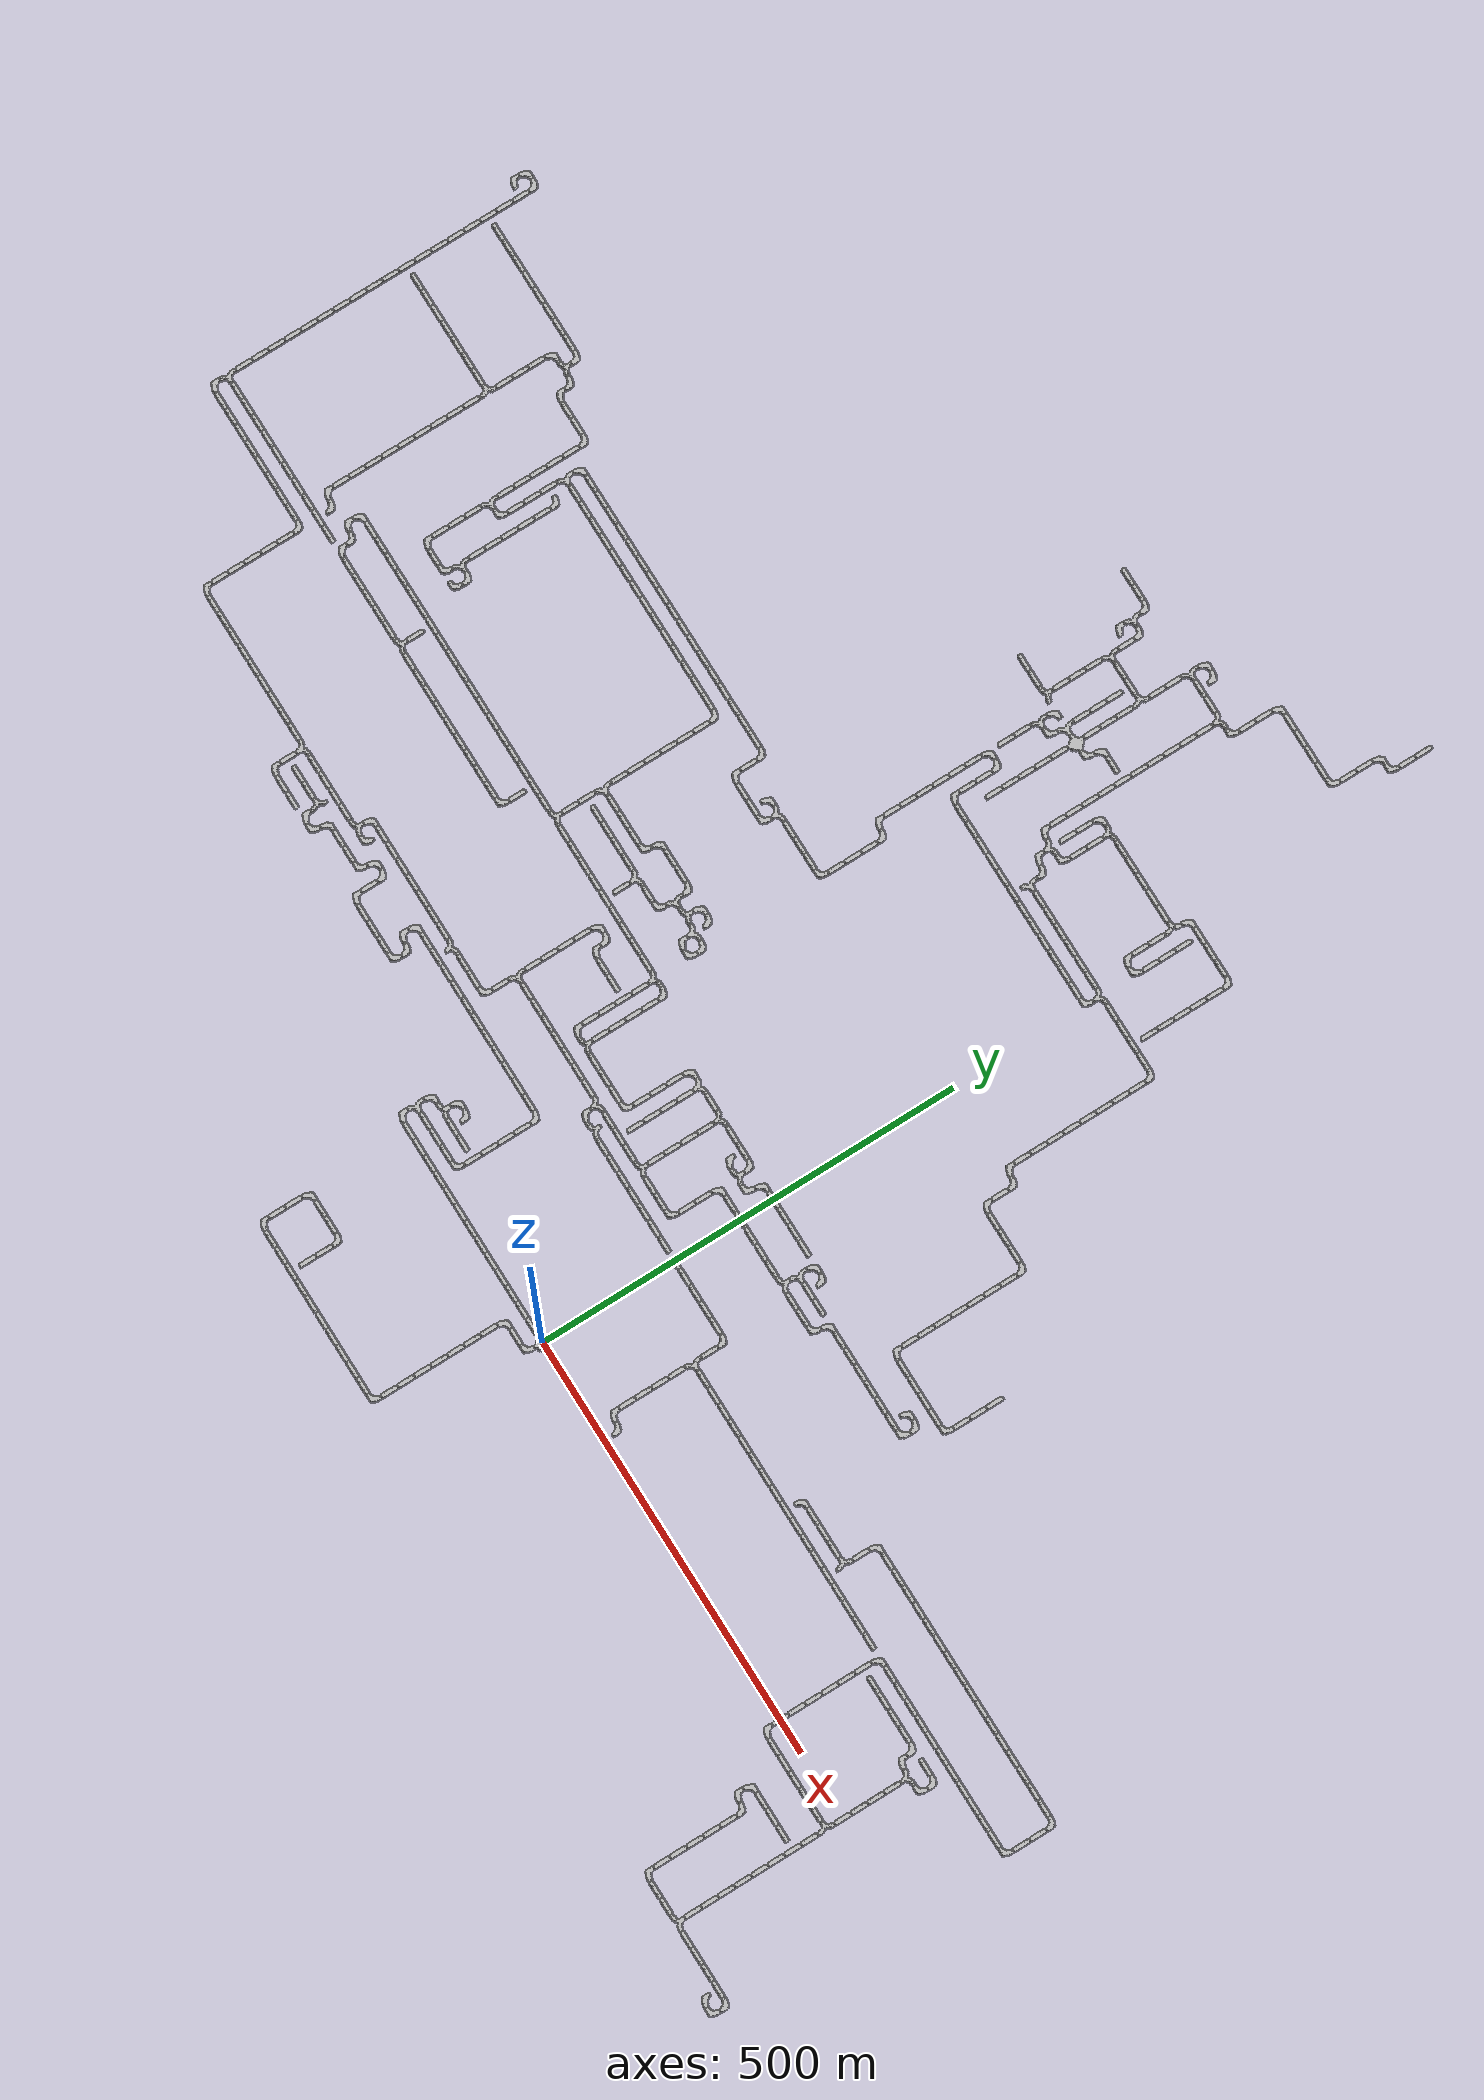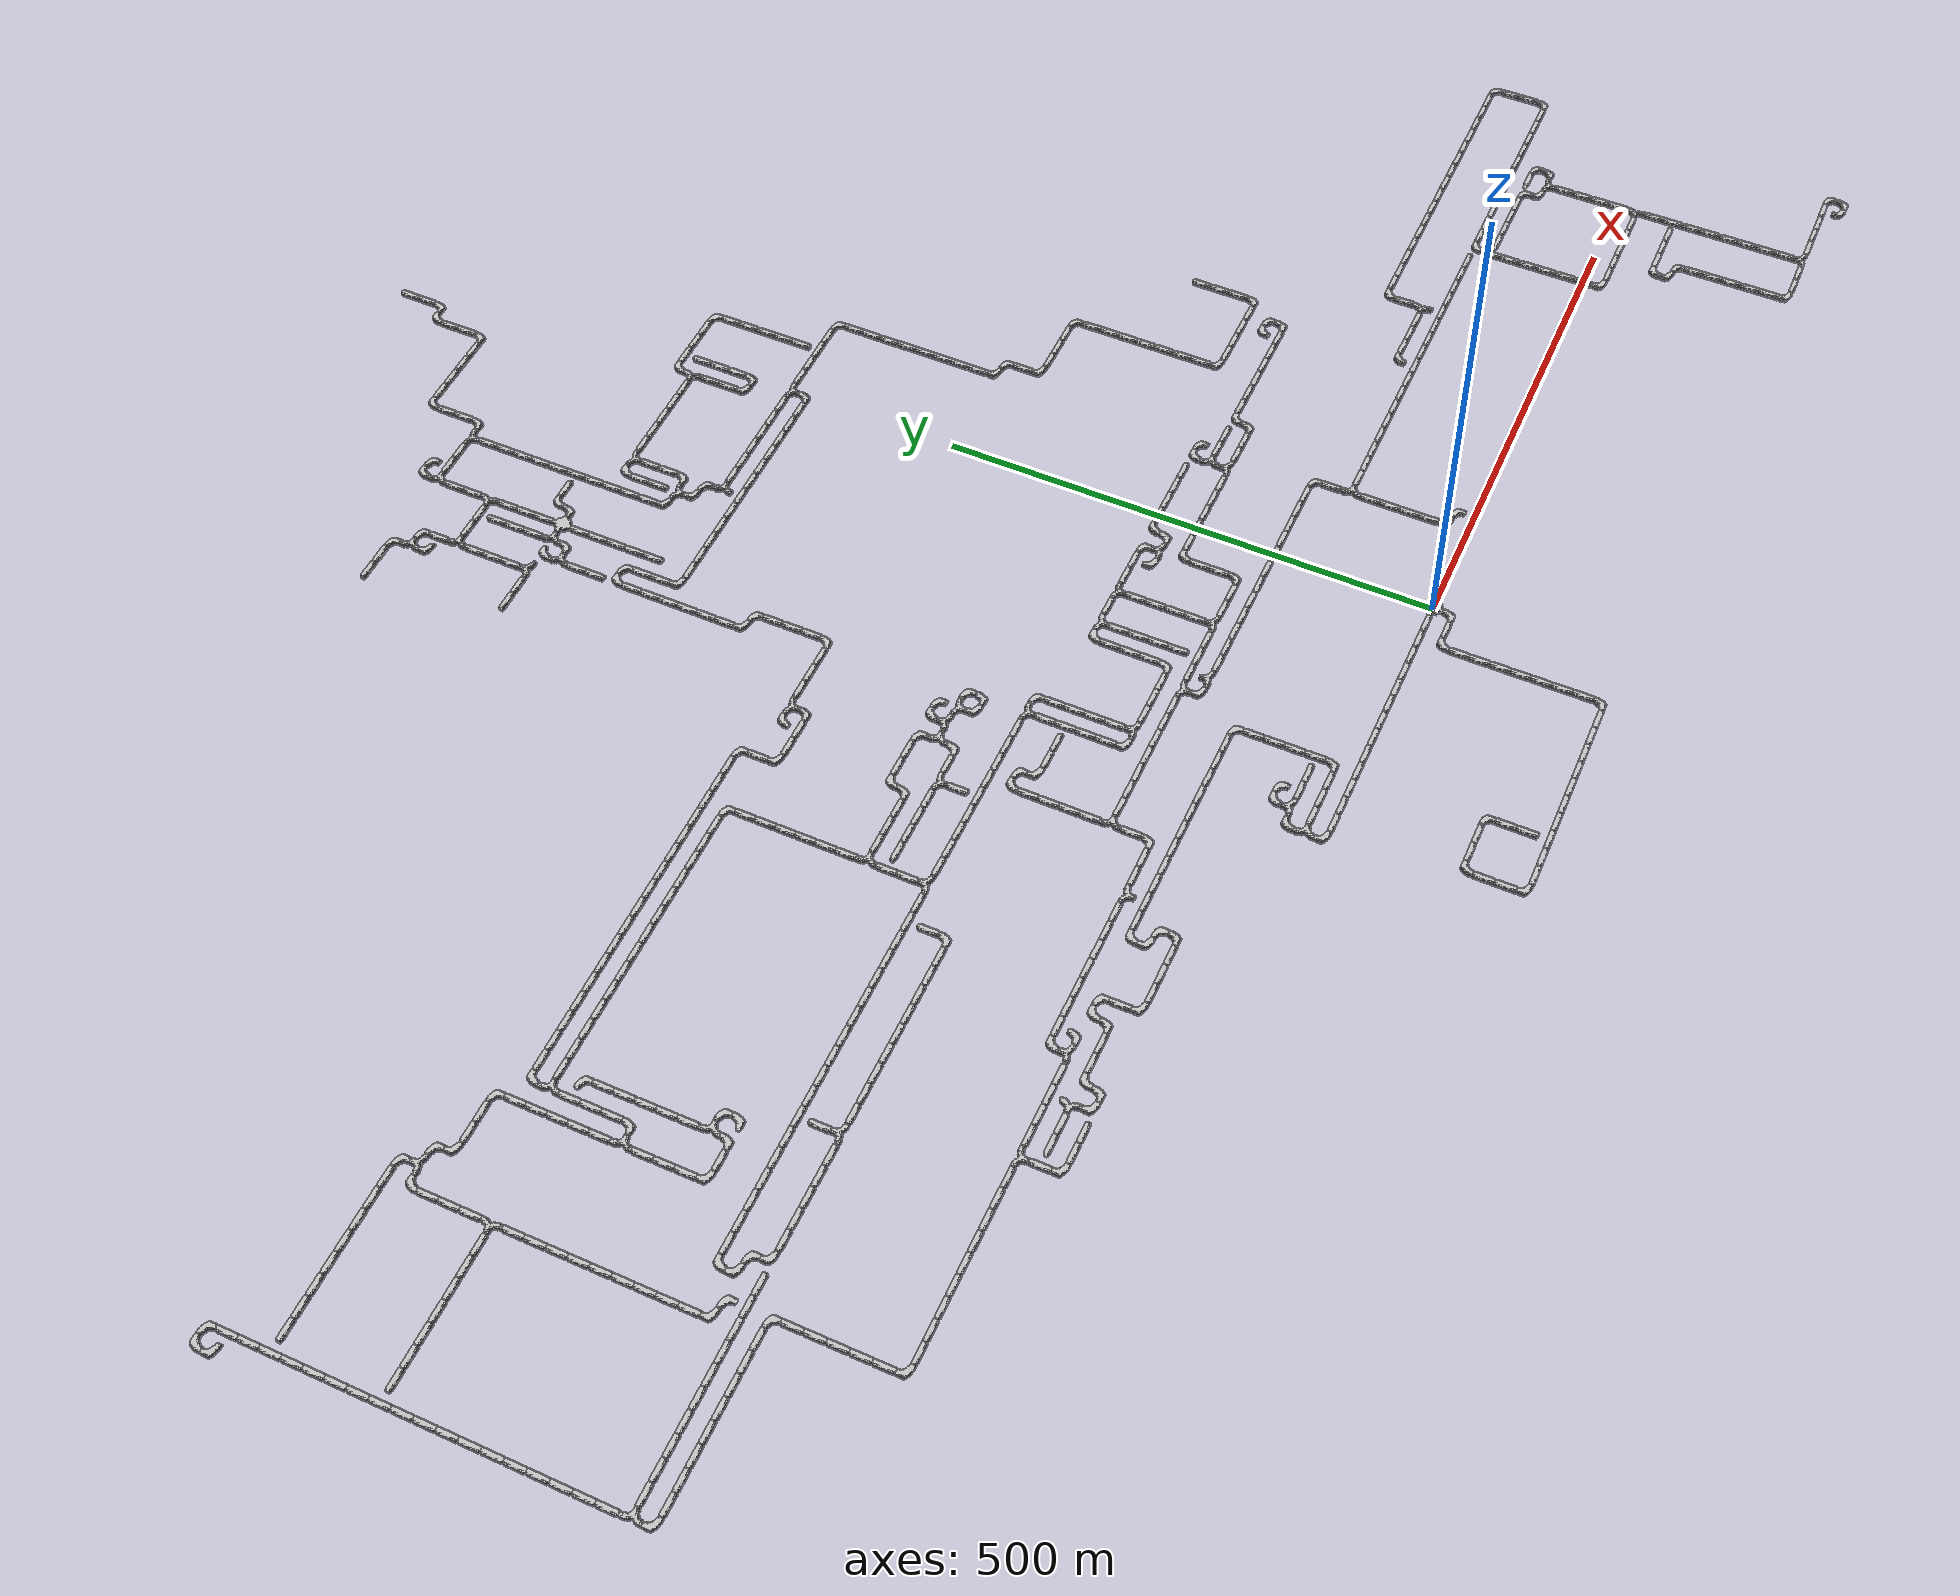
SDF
<sdf version="1.6">
<world name="cave_16000">
<include>
    <static>true</static>
    <name>cave_0_0</name>
    <pose>0 0 0 0 0 -1.5707963267948966</pose>
    <uri>model://cave_4way_20m</uri>
  </include>
  <include>
    <static>true</static>
    <name>cave_1_0</name>
    <pose>20 0 0 0 0 1.5707963267948966</pose>
    <uri>model://cave_straight_20m</uri>
  </include>
  <include>
    <static>true</static>
    <name>cave_2_0</name>
    <pose>40 0 0 0 0 1.5707963267948966</pose>
    <uri>model://cave_straight_20m</uri>
  </include>
  <include>
    <static>true</static>
    <name>cave_3_0</name>
    <pose>60 0 0 0 0 1.5707963267948966</pose>
    <uri>model://cave_straight_20m</uri>
  </include>
  <include>
    <static>true</static>
    <name>cave_4_0</name>
    <pose>80 0 0 0 0 1.5707963267948966</pose>
    <uri>model://cave_straight_20m</uri>
  </include>
  <include>
    <static>true</static>
    <name>cave_5_0</name>
    <pose>100 0 0 0 0 1.5707963267948966</pose>
    <uri>model://cave_straight_20m</uri>
  </include>
  <include>
    <static>true</static>
    <name>cave_6_0</name>
    <pose>120 0 0 0 0 1.5707963267948966</pose>
    <uri>model://cave_straight_20m</uri>
  </include>
  <include>
    <static>true</static>
    <name>cave_7_0</name>
    <pose>140 0 0 0 0 1.5707963267948966</pose>
    <uri>model://cave_straight_20m</uri>
  </include>
  <include>
    <static>true</static>
    <name>cave_8_0</name>
    <pose>160 0 0 0 0 1.5707963267948966</pose>
    <uri>model://cave_straight_20m</uri>
  </include>
  <include>
    <static>true</static>
    <name>cave_9_0</name>
    <pose>180 0 0 0 0 1.5707963267948966</pose>
    <uri>model://cave_straight_20m</uri>
  </include>
  <include>
    <static>true</static>
    <name>cave_10_0</name>
    <pose>200 0 0 0 0 1.5707963267948966</pose>
    <uri>model://cave_straight_20m</uri>
  </include>
  <include>
    <static>true</static>
    <name>cave_11_0</name>
    <pose>220 0 0 0 0 1.5707963267948966</pose>
    <uri>model://cave_straight_20m</uri>
  </include>
  <include>
    <static>true</static>
    <name>cave_12_0</name>
    <pose>240 0 0 0 0 1.5707963267948966</pose>
    <uri>model://cave_straight_20m</uri>
  </include>
  <include>
    <static>true</static>
    <name>cave_13_0</name>
    <pose>260 0 0 0 0 1.5707963267948966</pose>
    <uri>model://cave_straight_20m</uri>
  </include>
  <include>
    <static>true</static>
    <name>cave_14_0</name>
    <pose>280 0 0 0 0 1.5707963267948966</pose>
    <uri>model://cave_straight_20m</uri>
  </include>
  <include>
    <static>true</static>
    <name>cave_15_0</name>
    <pose>300 0 0 0 0 1.5707963267948966</pose>
    <uri>model://cave_straight_20m</uri>
  </include>
  <include>
    <static>true</static>
    <name>cave_16_0</name>
    <pose>320 0 0 0 0 1.5707963267948966</pose>
    <uri>model://cave_straight_20m</uri>
  </include>
  <include>
    <static>true</static>
    <name>cave_17_0</name>
    <pose>340 0 0 0 0 1.5707963267948966</pose>
    <uri>model://cave_straight_20m</uri>
  </include>
  <include>
    <static>true</static>
    <name>cave_18_0</name>
    <pose>360 0 0 0 0 1.5707963267948966</pose>
    <uri>model://cave_straight_20m</uri>
  </include>
  <include>
    <static>true</static>
    <name>cave_19_0</name>
    <pose>380 0 0 0 0 1.5707963267948966</pose>
    <uri>model://cave_straight_20m</uri>
  </include>
  <include>
    <static>true</static>
    <name>cave_20_0</name>
    <pose>400 0 0 0 0 1.5707963267948966</pose>
    <uri>model://cave_straight_20m</uri>
  </include>
  <include>
    <static>true</static>
    <name>cave_21_0</name>
    <pose>420 0 0 0 0 1.5707963267948966</pose>
    <uri>model://cave_straight_20m</uri>
  </include>
  <include>
    <static>true</static>
    <name>cave_22_0</name>
    <pose>440 0 0 0 0 1.5707963267948966</pose>
    <uri>model://cave_straight_20m</uri>
  </include>
  <include>
    <static>true</static>
    <name>cave_23_0</name>
    <pose>460 0 0 0 0 1.5707963267948966</pose>
    <uri>model://cave_3way_20m</uri>
  </include>
  <include>
    <static>true</static>
    <name>cave_23_-1</name>
    <pose>460 -20 0 0 0 0.0</pose>
    <uri>model://cave_L_20m</uri>
  </include>
  <include>
    <static>true</static>
    <name>cave_24_-1</name>
    <pose>480 -20 0 0 0 1.5707963267948966</pose>
    <uri>model://cave_straight_20m</uri>
  </include>
  <include>
    <static>true</static>
    <name>cave_25_-1</name>
    <pose>500 -20 0 0 0 1.5707963267948966</pose>
    <uri>model://cave_straight_20m</uri>
  </include>
  <include>
    <static>true</static>
    <name>cave_26_-1</name>
    <pose>520 -20 0 0 0 1.5707963267948966</pose>
    <uri>model://cave_straight_20m</uri>
  </include>
  <include>
    <static>true</static>
    <name>cave_27_-1</name>
    <pose>540 -20 0 0 0 1.5707963267948966</pose>
    <uri>model://cave_straight_20m</uri>
  </include>
  <include>
    <static>true</static>
    <name>cave_28_-1</name>
    <pose>560 -20 0 0 0 1.5707963267948966</pose>
    <uri>model://cave_straight_20m</uri>
  </include>
  <include>
    <static>true</static>
    <name>cave_29_-1</name>
    <pose>580 -20 0 0 0 1.5707963267948966</pose>
    <uri>model://cave_3way_20m</uri>
  </include>
  <include>
    <static>true</static>
    <name>cave_29_-2</name>
    <pose>580 -40 0 0 0 0.0</pose>
    <uri>model://cave_straight_20m</uri>
  </include>
  <include>
    <static>true</static>
    <name>cave_29_-3</name>
    <pose>580 -60 0 0 0 0.0</pose>
    <uri>model://cave_straight_20m</uri>
  </include>
  <include>
    <static>true</static>
    <name>cave_29_-4</name>
    <pose>580 -80 0 0 0 0.0</pose>
    <uri>model://cave_straight_20m</uri>
  </include>
  <include>
    <static>true</static>
    <name>cave_29_-5</name>
    <pose>580 -100 0 0 0 0.0</pose>
    <uri>model://cave_straight_20m</uri>
  </include>
  <include>
    <static>true</static>
    <name>cave_29_-6</name>
    <pose>580 -120 0 0 0 0.0</pose>
    <uri>model://cave_straight_20m</uri>
  </include>
  <include>
    <static>true</static>
    <name>cave_29_-7</name>
    <pose>580 -140 0 0 0 0.0</pose>
    <uri>model://cave_straight_20m</uri>
  </include>
  <include>
    <static>true</static>
    <name>cave_29_-8</name>
    <pose>580 -160 0 0 0 0.0</pose>
    <uri>model://cave_straight_20m</uri>
  </include>
  <include>
    <static>true</static>
    <name>cave_29_-9</name>
    <pose>580 -180 0 0 0 0.0</pose>
    <uri>model://cave_straight_20m</uri>
  </include>
  <include>
    <static>true</static>
    <name>cave_29_-10</name>
    <pose>580 -200 0 0 0 0.0</pose>
    <uri>model://cave_3way_20m</uri>
  </include>
  <include>
    <static>true</static>
    <name>cave_30_-10</name>
    <pose>600 -200 0 0 0 1.5707963267948966</pose>
    <uri>model://cave_straight_20m</uri>
  </include>
  <include>
    <static>true</static>
    <name>cave_31_-10</name>
    <pose>620 -200 0 0 0 1.5707963267948966</pose>
    <uri>model://cave_straight_20m</uri>
  </include>
  <include>
    <static>true</static>
    <name>cave_32_-10</name>
    <pose>640 -200 0 0 0 1.5707963267948966</pose>
    <uri>model://cave_straight_20m</uri>
  </include>
  <include>
    <static>true</static>
    <name>cave_33_-10</name>
    <pose>660 -200 0 0 0 1.5707963267948966</pose>
    <uri>model://cave_straight_20m</uri>
  </include>
  <include>
    <static>true</static>
    <name>cave_34_-10</name>
    <pose>680 -200 0 0 0 3.141592653589793</pose>
    <uri>model://cave_L_20m</uri>
  </include>
  <include>
    <static>true</static>
    <name>cave_34_-11</name>
    <pose>680 -220 0 0 0 1.5707963267948966</pose>
    <uri>model://cave_L_20m</uri>
  </include>
  <include>
    <static>true</static>
    <name>cave_33_-11</name>
    <pose>660 -220 0 0 0 0.0</pose>
    <uri>model://cave_L_20m</uri>
  </include>
  <include>
    <static>true</static>
    <name>cave_28_-10</name>
    <pose>560 -200 0 0 0 1.5707963267948966</pose>
    <uri>model://cave_straight_20m</uri>
  </include>
  <include>
    <static>true</static>
    <name>cave_27_-10</name>
    <pose>540 -200 0 0 0 1.5707963267948966</pose>
    <uri>model://cave_straight_20m</uri>
  </include>
  <include>
    <static>true</static>
    <name>cave_26_-10</name>
    <pose>520 -200 0 0 0 0.0</pose>
    <uri>model://cave_L_20m</uri>
  </include>
  <include>
    <static>true</static>
    <name>cave_26_-9</name>
    <pose>520 -180 0 0 0 0.0</pose>
    <uri>model://cave_straight_20m</uri>
  </include>
  <include>
    <static>true</static>
    <name>cave_26_-8</name>
    <pose>520 -160 0 0 0 0.0</pose>
    <uri>model://cave_straight_20m</uri>
  </include>
  <include>
    <static>true</static>
    <name>cave_26_-7</name>
    <pose>520 -140 0 0 0 0.0</pose>
    <uri>model://cave_straight_20m</uri>
  </include>
  <include>
    <static>true</static>
    <name>cave_26_-6</name>
    <pose>520 -120 0 0 0 0.0</pose>
    <uri>model://cave_straight_20m</uri>
  </include>
  <include>
    <static>true</static>
    <name>cave_26_-5</name>
    <pose>520 -100 0 0 0 0.0</pose>
    <uri>model://cave_straight_20m</uri>
  </include>
  <include>
    <static>true</static>
    <name>cave_26_-4</name>
    <pose>520 -80 0 0 0 3.141592653589793</pose>
    <uri>model://cave_L_20m</uri>
  </include>
  <include>
    <static>true</static>
    <name>cave_25_-4</name>
    <pose>500 -80 0 0 0 0.0</pose>
    <uri>model://cave_L_20m</uri>
  </include>
  <include>
    <static>true</static>
    <name>cave_25_-3</name>
    <pose>500 -60 0 0 0 -1.5707963267948966</pose>
    <uri>model://cave_L_20m</uri>
  </include>
  <include>
    <static>true</static>
    <name>cave_26_-3</name>
    <pose>520 -60 0 0 0 1.5707963267948966</pose>
    <uri>model://cave_straight_20m</uri>
  </include>
  <include>
    <static>true</static>
    <name>cave_27_-3</name>
    <pose>540 -60 0 0 0 1.5707963267948966</pose>
    <uri>model://cave_straight_20m</uri>
  </include>
  <include>
    <static>true</static>
    <name>cave_28_-3</name>
    <pose>560 -60 0 0 0 1.5707963267948966</pose>
    <uri>model://cave_straight_20m</uri>
  </include>
  <include>
    <static>true</static>
    <name>cave_29_0</name>
    <pose>580 0 0 0 0 0.0</pose>
    <uri>model://cave_straight_20m</uri>
  </include>
  <include>
    <static>true</static>
    <name>cave_29_1</name>
    <pose>580 20 0 0 0 0.0</pose>
    <uri>model://cave_straight_20m</uri>
  </include>
  <include>
    <static>true</static>
    <name>cave_29_2</name>
    <pose>580 40 0 0 0 0.0</pose>
    <uri>model://cave_straight_20m</uri>
  </include>
  <include>
    <static>true</static>
    <name>cave_29_3</name>
    <pose>580 60 0 0 0 0.0</pose>
    <uri>model://cave_straight_20m</uri>
  </include>
  <include>
    <static>true</static>
    <name>cave_29_4</name>
    <pose>580 80 0 0 0 3.141592653589793</pose>
    <uri>model://cave_3way_20m</uri>
  </include>
  <include>
    <static>true</static>
    <name>cave_30_4</name>
    <pose>600 80 0 0 0 1.5707963267948966</pose>
    <uri>model://cave_L_20m</uri>
  </include>
  <include>
    <static>true</static>
    <name>cave_30_5</name>
    <pose>600 100 0 0 0 3.141592653589793</pose>
    <uri>model://cave_L_20m</uri>
  </include>
  <include>
    <static>true</static>
    <name>cave_29_5</name>
    <pose>580 100 0 0 0 1.5707963267948966</pose>
    <uri>model://cave_straight_20m</uri>
  </include>
  <include>
    <static>true</static>
    <name>cave_28_4</name>
    <pose>560 80 0 0 0 0.0</pose>
    <uri>model://cave_L_20m</uri>
  </include>
  <include>
    <static>true</static>
    <name>cave_28_5</name>
    <pose>560 100 0 0 0 3.141592653589793</pose>
    <uri>model://cave_L_20m</uri>
  </include>
  <include>
    <static>true</static>
    <name>cave_27_5</name>
    <pose>540 100 0 0 0 1.5707963267948966</pose>
    <uri>model://cave_straight_20m</uri>
  </include>
  <include>
    <static>true</static>
    <name>cave_26_5</name>
    <pose>520 100 0 0 0 1.5707963267948966</pose>
    <uri>model://cave_straight_20m</uri>
  </include>
  <include>
    <static>true</static>
    <name>cave_25_5</name>
    <pose>500 100 0 0 0 1.5707963267948966</pose>
    <uri>model://cave_straight_20m</uri>
  </include>
  <include>
    <static>true</static>
    <name>cave_24_5</name>
    <pose>480 100 0 0 0 1.5707963267948966</pose>
    <uri>model://cave_straight_20m</uri>
  </include>
  <include>
    <static>true</static>
    <name>cave_23_1</name>
    <pose>460 20 0 0 0 0.0</pose>
    <uri>model://cave_straight_20m</uri>
  </include>
  <include>
    <static>true</static>
    <name>cave_23_2</name>
    <pose>460 40 0 0 0 0.0</pose>
    <uri>model://cave_straight_20m</uri>
  </include>
  <include>
    <static>true</static>
    <name>cave_23_3</name>
    <pose>460 60 0 0 0 0.0</pose>
    <uri>model://cave_straight_20m</uri>
  </include>
  <include>
    <static>true</static>
    <name>cave_23_4</name>
    <pose>460 80 0 0 0 0.0</pose>
    <uri>model://cave_straight_20m</uri>
  </include>
  <include>
    <static>true</static>
    <name>cave_23_5</name>
    <pose>460 100 0 0 0 0.0</pose>
    <uri>model://cave_straight_20m</uri>
  </include>
  <include>
    <static>true</static>
    <name>cave_23_6</name>
    <pose>460 120 0 0 0 -1.5707963267948966</pose>
    <uri>model://cave_L_20m</uri>
  </include>
  <include>
    <static>true</static>
    <name>cave_24_6</name>
    <pose>480 120 0 0 0 1.5707963267948966</pose>
    <uri>model://cave_straight_20m</uri>
  </include>
  <include>
    <static>true</static>
    <name>cave_25_6</name>
    <pose>500 120 0 0 0 1.5707963267948966</pose>
    <uri>model://cave_straight_20m</uri>
  </include>
  <include>
    <static>true</static>
    <name>cave_26_6</name>
    <pose>520 120 0 0 0 1.5707963267948966</pose>
    <uri>model://cave_straight_20m</uri>
  </include>
  <include>
    <static>true</static>
    <name>cave_27_6</name>
    <pose>540 120 0 0 0 1.5707963267948966</pose>
    <uri>model://cave_straight_20m</uri>
  </include>
  <include>
    <static>true</static>
    <name>cave_28_6</name>
    <pose>560 120 0 0 0 1.5707963267948966</pose>
    <uri>model://cave_straight_20m</uri>
  </include>
  <include>
    <static>true</static>
    <name>cave_29_6</name>
    <pose>580 120 0 0 0 1.5707963267948966</pose>
    <uri>model://cave_straight_20m</uri>
  </include>
  <include>
    <static>true</static>
    <name>cave_30_6</name>
    <pose>600 120 0 0 0 1.5707963267948966</pose>
    <uri>model://cave_straight_20m</uri>
  </include>
  <include>
    <static>true</static>
    <name>cave_31_6</name>
    <pose>620 120 0 0 0 1.5707963267948966</pose>
    <uri>model://cave_straight_20m</uri>
  </include>
  <include>
    <static>true</static>
    <name>cave_32_6</name>
    <pose>640 120 0 0 0 1.5707963267948966</pose>
    <uri>model://cave_straight_20m</uri>
  </include>
  <include>
    <static>true</static>
    <name>cave_33_6</name>
    <pose>660 120 0 0 0 1.5707963267948966</pose>
    <uri>model://cave_straight_20m</uri>
  </include>
  <include>
    <static>true</static>
    <name>cave_34_6</name>
    <pose>680 120 0 0 0 1.5707963267948966</pose>
    <uri>model://cave_straight_20m</uri>
  </include>
  <include>
    <static>true</static>
    <name>cave_35_6</name>
    <pose>700 120 0 0 0 1.5707963267948966</pose>
    <uri>model://cave_L_20m</uri>
  </include>
  <include>
    <static>true</static>
    <name>cave_35_7</name>
    <pose>700 140 0 0 0 0.0</pose>
    <uri>model://cave_straight_20m</uri>
  </include>
  <include>
    <static>true</static>
    <name>cave_35_8</name>
    <pose>700 160 0 0 0 0.0</pose>
    <uri>model://cave_straight_20m</uri>
  </include>
  <include>
    <static>true</static>
    <name>cave_35_9</name>
    <pose>700 180 0 0 0 3.141592653589793</pose>
    <uri>model://cave_L_20m</uri>
  </include>
  <include>
    <static>true</static>
    <name>cave_34_9</name>
    <pose>680 180 0 0 0 1.5707963267948966</pose>
    <uri>model://cave_straight_20m</uri>
  </include>
  <include>
    <static>true</static>
    <name>cave_33_9</name>
    <pose>660 180 0 0 0 1.5707963267948966</pose>
    <uri>model://cave_straight_20m</uri>
  </include>
  <include>
    <static>true</static>
    <name>cave_32_9</name>
    <pose>640 180 0 0 0 1.5707963267948966</pose>
    <uri>model://cave_straight_20m</uri>
  </include>
  <include>
    <static>true</static>
    <name>cave_31_9</name>
    <pose>620 180 0 0 0 1.5707963267948966</pose>
    <uri>model://cave_straight_20m</uri>
  </include>
  <include>
    <static>true</static>
    <name>cave_30_9</name>
    <pose>600 180 0 0 0 1.5707963267948966</pose>
    <uri>model://cave_straight_20m</uri>
  </include>
  <include>
    <static>true</static>
    <name>cave_29_9</name>
    <pose>580 180 0 0 0 1.5707963267948966</pose>
    <uri>model://cave_straight_20m</uri>
  </include>
  <include>
    <static>true</static>
    <name>cave_28_9</name>
    <pose>560 180 0 0 0 1.5707963267948966</pose>
    <uri>model://cave_straight_20m</uri>
  </include>
  <include>
    <static>true</static>
    <name>cave_27_9</name>
    <pose>540 180 0 0 0 1.5707963267948966</pose>
    <uri>model://cave_straight_20m</uri>
  </include>
  <include>
    <static>true</static>
    <name>cave_26_9</name>
    <pose>520 180 0 0 0 1.5707963267948966</pose>
    <uri>model://cave_straight_20m</uri>
  </include>
  <include>
    <static>true</static>
    <name>cave_25_9</name>
    <pose>500 180 0 0 0 1.5707963267948966</pose>
    <uri>model://cave_straight_20m</uri>
  </include>
  <include>
    <static>true</static>
    <name>cave_24_9</name>
    <pose>480 180 0 0 0 1.5707963267948966</pose>
    <uri>model://cave_straight_20m</uri>
  </include>
  <include>
    <static>true</static>
    <name>cave_23_9</name>
    <pose>460 180 0 0 0 1.5707963267948966</pose>
    <uri>model://cave_straight_20m</uri>
  </include>
  <include>
    <static>true</static>
    <name>cave_22_9</name>
    <pose>440 180 0 0 0 1.5707963267948966</pose>
    <uri>model://cave_straight_20m</uri>
  </include>
  <include>
    <static>true</static>
    <name>cave_21_9</name>
    <pose>420 180 0 0 0 1.5707963267948966</pose>
    <uri>model://cave_straight_20m</uri>
  </include>
  <include>
    <static>true</static>
    <name>cave_20_9</name>
    <pose>400 180 0 0 0 1.5707963267948966</pose>
    <uri>model://cave_straight_20m</uri>
  </include>
  <include>
    <static>true</static>
    <name>cave_19_9</name>
    <pose>380 180 0 0 0 1.5707963267948966</pose>
    <uri>model://cave_straight_20m</uri>
  </include>
  <include>
    <static>true</static>
    <name>cave_18_9</name>
    <pose>360 180 0 0 0 -1.5707963267948966</pose>
    <uri>model://cave_L_20m</uri>
  </include>
  <include>
    <static>true</static>
    <name>cave_18_8</name>
    <pose>360 160 0 0 0 0.0</pose>
    <uri>model://cave_straight_20m</uri>
  </include>
  <include>
    <static>true</static>
    <name>cave_18_7</name>
    <pose>360 140 0 0 0 1.5707963267948966</pose>
    <uri>model://cave_3way_20m</uri>
  </include>
  <include>
    <static>true</static>
    <name>cave_17_7</name>
    <pose>340 140 0 0 0 1.5707963267948966</pose>
    <uri>model://cave_straight_20m</uri>
  </include>
  <include>
    <static>true</static>
    <name>cave_16_7</name>
    <pose>320 140 0 0 0 1.5707963267948966</pose>
    <uri>model://cave_straight_20m</uri>
  </include>
  <include>
    <static>true</static>
    <name>cave_15_7</name>
    <pose>300 140 0 0 0 1.5707963267948966</pose>
    <uri>model://cave_straight_20m</uri>
  </include>
  <include>
    <static>true</static>
    <name>cave_14_7</name>
    <pose>280 140 0 0 0 -1.5707963267948966</pose>
    <uri>model://cave_L_20m</uri>
  </include>
  <include>
    <static>true</static>
    <name>cave_0_-1</name>
    <pose>0 -20 0 0 0 1.5707963267948966</pose>
    <uri>model://cave_L_20m</uri>
  </include>
  <include>
    <static>true</static>
    <name>cave_-1_-1</name>
    <pose>-20 -20 0 0 0 1.5707963267948966</pose>
    <uri>model://cave_straight_20m</uri>
  </include>
  <include>
    <static>true</static>
    <name>cave_-2_-1</name>
    <pose>-40 -20 0 0 0 -1.5707963267948966</pose>
    <uri>model://cave_L_20m</uri>
  </include>
  <include>
    <static>true</static>
    <name>cave_-2_-2</name>
    <pose>-40 -40 0 0 0 0.0</pose>
    <uri>model://cave_straight_20m</uri>
  </include>
  <include>
    <static>true</static>
    <name>cave_-2_-3</name>
    <pose>-40 -60 0 0 0 0.0</pose>
    <uri>model://cave_straight_20m</uri>
  </include>
  <include>
    <static>true</static>
    <name>cave_-2_-4</name>
    <pose>-40 -80 0 0 0 0.0</pose>
    <uri>model://cave_straight_20m</uri>
  </include>
  <include>
    <static>true</static>
    <name>cave_-2_-5</name>
    <pose>-40 -100 0 0 0 0.0</pose>
    <uri>model://cave_straight_20m</uri>
  </include>
  <include>
    <static>true</static>
    <name>cave_-2_-6</name>
    <pose>-40 -120 0 0 0 0.0</pose>
    <uri>model://cave_straight_20m</uri>
  </include>
  <include>
    <static>true</static>
    <name>cave_-2_-7</name>
    <pose>-40 -140 0 0 0 0.0</pose>
    <uri>model://cave_straight_20m</uri>
  </include>
  <include>
    <static>true</static>
    <name>cave_-2_-8</name>
    <pose>-40 -160 0 0 0 0.0</pose>
    <uri>model://cave_straight_20m</uri>
  </include>
  <include>
    <static>true</static>
    <name>cave_-2_-9</name>
    <pose>-40 -180 0 0 0 1.5707963267948966</pose>
    <uri>model://cave_L_20m</uri>
  </include>
  <include>
    <static>true</static>
    <name>cave_-3_-9</name>
    <pose>-60 -180 0 0 0 1.5707963267948966</pose>
    <uri>model://cave_straight_20m</uri>
  </include>
  <include>
    <static>true</static>
    <name>cave_-4_-9</name>
    <pose>-80 -180 0 0 0 1.5707963267948966</pose>
    <uri>model://cave_straight_20m</uri>
  </include>
  <include>
    <static>true</static>
    <name>cave_-5_-9</name>
    <pose>-100 -180 0 0 0 1.5707963267948966</pose>
    <uri>model://cave_straight_20m</uri>
  </include>
  <include>
    <static>true</static>
    <name>cave_-6_-9</name>
    <pose>-120 -180 0 0 0 1.5707963267948966</pose>
    <uri>model://cave_straight_20m</uri>
  </include>
  <include>
    <static>true</static>
    <name>cave_-7_-9</name>
    <pose>-140 -180 0 0 0 1.5707963267948966</pose>
    <uri>model://cave_straight_20m</uri>
  </include>
  <include>
    <static>true</static>
    <name>cave_-8_-9</name>
    <pose>-160 -180 0 0 0 1.5707963267948966</pose>
    <uri>model://cave_straight_20m</uri>
  </include>
  <include>
    <static>true</static>
    <name>cave_-9_-9</name>
    <pose>-180 -180 0 0 0 1.5707963267948966</pose>
    <uri>model://cave_straight_20m</uri>
  </include>
  <include>
    <static>true</static>
    <name>cave_-10_-9</name>
    <pose>-200 -180 0 0 0 1.5707963267948966</pose>
    <uri>model://cave_straight_20m</uri>
  </include>
  <include>
    <static>true</static>
    <name>cave_-11_-9</name>
    <pose>-220 -180 0 0 0 1.5707963267948966</pose>
    <uri>model://cave_straight_20m</uri>
  </include>
  <include>
    <static>true</static>
    <name>cave_-12_-9</name>
    <pose>-240 -180 0 0 0 1.5707963267948966</pose>
    <uri>model://cave_straight_20m</uri>
  </include>
  <include>
    <static>true</static>
    <name>cave_-13_-9</name>
    <pose>-260 -180 0 0 0 0.0</pose>
    <uri>model://cave_L_20m</uri>
  </include>
  <include>
    <static>true</static>
    <name>cave_-13_-8</name>
    <pose>-260 -160 0 0 0 0.0</pose>
    <uri>model://cave_straight_20m</uri>
  </include>
  <include>
    <static>true</static>
    <name>cave_-13_-7</name>
    <pose>-260 -140 0 0 0 0.0</pose>
    <uri>model://cave_straight_20m</uri>
  </include>
  <include>
    <static>true</static>
    <name>cave_-13_-6</name>
    <pose>-260 -120 0 0 0 -1.5707963267948966</pose>
    <uri>model://cave_L_20m</uri>
  </include>
  <include>
    <static>true</static>
    <name>cave_-12_-6</name>
    <pose>-240 -120 0 0 0 1.5707963267948966</pose>
    <uri>model://cave_straight_20m</uri>
  </include>
  <include>
    <static>true</static>
    <name>cave_-11_-6</name>
    <pose>-220 -120 0 0 0 1.5707963267948966</pose>
    <uri>model://cave_straight_20m</uri>
  </include>
  <include>
    <static>true</static>
    <name>cave_-10_-6</name>
    <pose>-200 -120 0 0 0 3.141592653589793</pose>
    <uri>model://cave_L_20m</uri>
  </include>
  <include>
    <static>true</static>
    <name>cave_-10_-7</name>
    <pose>-200 -140 0 0 0 0.0</pose>
    <uri>model://cave_straight_20m</uri>
  </include>
  <include>
    <static>true</static>
    <name>cave_-10_-8</name>
    <pose>-200 -160 0 0 0 0.0</pose>
    <uri>model://cave_straight_20m</uri>
  </include>
  <include>
    <static>true</static>
    <name>cave_-1_0</name>
    <pose>-20 0 0 0 0 1.5707963267948966</pose>
    <uri>model://cave_straight_20m</uri>
  </include>
  <include>
    <static>true</static>
    <name>cave_-2_0</name>
    <pose>-40 0 0 0 0 1.5707963267948966</pose>
    <uri>model://cave_straight_20m</uri>
  </include>
  <include>
    <static>true</static>
    <name>cave_-3_0</name>
    <pose>-60 0 0 0 0 1.5707963267948966</pose>
    <uri>model://cave_straight_20m</uri>
  </include>
  <include>
    <static>true</static>
    <name>cave_-4_0</name>
    <pose>-80 0 0 0 0 1.5707963267948966</pose>
    <uri>model://cave_straight_20m</uri>
  </include>
  <include>
    <static>true</static>
    <name>cave_-5_0</name>
    <pose>-100 0 0 0 0 1.5707963267948966</pose>
    <uri>model://cave_straight_20m</uri>
  </include>
  <include>
    <static>true</static>
    <name>cave_-6_0</name>
    <pose>-120 0 0 0 0 1.5707963267948966</pose>
    <uri>model://cave_straight_20m</uri>
  </include>
  <include>
    <static>true</static>
    <name>cave_-7_0</name>
    <pose>-140 0 0 0 0 1.5707963267948966</pose>
    <uri>model://cave_straight_20m</uri>
  </include>
  <include>
    <static>true</static>
    <name>cave_-8_0</name>
    <pose>-160 0 0 0 0 1.5707963267948966</pose>
    <uri>model://cave_straight_20m</uri>
  </include>
  <include>
    <static>true</static>
    <name>cave_-9_0</name>
    <pose>-180 0 0 0 0 1.5707963267948966</pose>
    <uri>model://cave_straight_20m</uri>
  </include>
  <include>
    <static>true</static>
    <name>cave_-10_0</name>
    <pose>-200 0 0 0 0 1.5707963267948966</pose>
    <uri>model://cave_straight_20m</uri>
  </include>
  <include>
    <static>true</static>
    <name>cave_-11_0</name>
    <pose>-220 0 0 0 0 1.5707963267948966</pose>
    <uri>model://cave_straight_20m</uri>
  </include>
  <include>
    <static>true</static>
    <name>cave_-12_0</name>
    <pose>-240 0 0 0 0 1.5707963267948966</pose>
    <uri>model://cave_straight_20m</uri>
  </include>
  <include>
    <static>true</static>
    <name>cave_-13_0</name>
    <pose>-260 0 0 0 0 1.5707963267948966</pose>
    <uri>model://cave_straight_20m</uri>
  </include>
  <include>
    <static>true</static>
    <name>cave_-14_0</name>
    <pose>-280 0 0 0 0 0.0</pose>
    <uri>model://cave_L_20m</uri>
  </include>
  <include>
    <static>true</static>
    <name>cave_-14_1</name>
    <pose>-280 20 0 0 0 -1.5707963267948966</pose>
    <uri>model://cave_3way_20m</uri>
  </include>
  <include>
    <static>true</static>
    <name>cave_-13_1</name>
    <pose>-260 20 0 0 0 1.5707963267948966</pose>
    <uri>model://cave_straight_20m</uri>
  </include>
  <include>
    <static>true</static>
    <name>cave_-12_1</name>
    <pose>-240 20 0 0 0 1.5707963267948966</pose>
    <uri>model://cave_straight_20m</uri>
  </include>
  <include>
    <static>true</static>
    <name>cave_-11_1</name>
    <pose>-220 20 0 0 0 1.5707963267948966</pose>
    <uri>model://cave_straight_20m</uri>
  </include>
  <include>
    <static>true</static>
    <name>cave_-10_1</name>
    <pose>-200 20 0 0 0 1.5707963267948966</pose>
    <uri>model://cave_L_20m</uri>
  </include>
  <include>
    <static>true</static>
    <name>cave_-10_2</name>
    <pose>-200 40 0 0 0 0.0</pose>
    <uri>model://cave_straight_20m</uri>
  </include>
  <include>
    <static>true</static>
    <name>cave_-10_3</name>
    <pose>-200 60 0 0 0 0.0</pose>
    <uri>model://cave_straight_20m</uri>
  </include>
  <include>
    <static>true</static>
    <name>cave_-10_4</name>
    <pose>-200 80 0 0 0 0.0</pose>
    <uri>model://cave_straight_20m</uri>
  </include>
  <include>
    <static>true</static>
    <name>cave_-10_5</name>
    <pose>-200 100 0 0 0 0.0</pose>
    <uri>model://cave_straight_20m</uri>
  </include>
  <include>
    <static>true</static>
    <name>cave_-10_6</name>
    <pose>-200 120 0 0 0 3.141592653589793</pose>
    <uri>model://cave_L_20m</uri>
  </include>
  <include>
    <static>true</static>
    <name>cave_-11_6</name>
    <pose>-220 120 0 0 0 1.5707963267948966</pose>
    <uri>model://cave_straight_20m</uri>
  </include>
  <include>
    <static>true</static>
    <name>cave_-12_6</name>
    <pose>-240 120 0 0 0 1.5707963267948966</pose>
    <uri>model://cave_straight_20m</uri>
  </include>
  <include>
    <static>true</static>
    <name>cave_-13_6</name>
    <pose>-260 120 0 0 0 1.5707963267948966</pose>
    <uri>model://cave_straight_20m</uri>
  </include>
  <include>
    <static>true</static>
    <name>cave_-14_6</name>
    <pose>-280 120 0 0 0 1.5707963267948966</pose>
    <uri>model://cave_straight_20m</uri>
  </include>
  <include>
    <static>true</static>
    <name>cave_-15_6</name>
    <pose>-300 120 0 0 0 1.5707963267948966</pose>
    <uri>model://cave_straight_20m</uri>
  </include>
  <include>
    <static>true</static>
    <name>cave_-16_6</name>
    <pose>-320 120 0 0 0 1.5707963267948966</pose>
    <uri>model://cave_straight_20m</uri>
  </include>
  <include>
    <static>true</static>
    <name>cave_-17_6</name>
    <pose>-340 120 0 0 0 1.5707963267948966</pose>
    <uri>model://cave_straight_20m</uri>
  </include>
  <include>
    <static>true</static>
    <name>cave_-18_6</name>
    <pose>-360 120 0 0 0 1.5707963267948966</pose>
    <uri>model://cave_straight_20m</uri>
  </include>
  <include>
    <static>true</static>
    <name>cave_-19_6</name>
    <pose>-380 120 0 0 0 1.5707963267948966</pose>
    <uri>model://cave_straight_20m</uri>
  </include>
  <include>
    <static>true</static>
    <name>cave_-20_6</name>
    <pose>-400 120 0 0 0 1.5707963267948966</pose>
    <uri>model://cave_straight_20m</uri>
  </include>
  <include>
    <static>true</static>
    <name>cave_-21_6</name>
    <pose>-420 120 0 0 0 1.5707963267948966</pose>
    <uri>model://cave_straight_20m</uri>
  </include>
  <include>
    <static>true</static>
    <name>cave_-22_6</name>
    <pose>-440 120 0 0 0 -1.5707963267948966</pose>
    <uri>model://cave_L_20m</uri>
  </include>
  <include>
    <static>true</static>
    <name>cave_-22_5</name>
    <pose>-440 100 0 0 0 0.0</pose>
    <uri>model://cave_L_20m</uri>
  </include>
  <include>
    <static>true</static>
    <name>cave_-21_5</name>
    <pose>-420 100 0 0 0 3.141592653589793</pose>
    <uri>model://cave_L_20m</uri>
  </include>
  <include>
    <static>true</static>
    <name>cave_-21_4</name>
    <pose>-420 80 0 0 0 1.5707963267948966</pose>
    <uri>model://cave_L_20m</uri>
  </include>
  <include>
    <static>true</static>
    <name>cave_-22_4</name>
    <pose>-440 80 0 0 0 1.5707963267948966</pose>
    <uri>model://cave_straight_20m</uri>
  </include>
  <include>
    <static>true</static>
    <name>cave_-23_4</name>
    <pose>-460 80 0 0 0 1.5707963267948966</pose>
    <uri>model://cave_straight_20m</uri>
  </include>
  <include>
    <static>true</static>
    <name>cave_-24_4</name>
    <pose>-480 80 0 0 0 1.5707963267948966</pose>
    <uri>model://cave_straight_20m</uri>
  </include>
  <include>
    <static>true</static>
    <name>cave_-25_4</name>
    <pose>-500 80 0 0 0 0.0</pose>
    <uri>model://cave_L_20m</uri>
  </include>
  <include>
    <static>true</static>
    <name>cave_-25_5</name>
    <pose>-500 100 0 0 0 0.0</pose>
    <uri>model://cave_straight_20m</uri>
  </include>
  <include>
    <static>true</static>
    <name>cave_-25_6</name>
    <pose>-500 120 0 0 0 3.141592653589793</pose>
    <uri>model://cave_L_20m</uri>
  </include>
  <include>
    <static>true</static>
    <name>cave_-26_6</name>
    <pose>-520 120 0 0 0 -1.5707963267948966</pose>
    <uri>model://cave_L_20m</uri>
  </include>
  <include>
    <static>true</static>
    <name>cave_-26_5</name>
    <pose>-520 100 0 0 0 1.5707963267948966</pose>
    <uri>model://cave_L_20m</uri>
  </include>
  <include>
    <static>true</static>
    <name>cave_-27_5</name>
    <pose>-540 100 0 0 0 1.5707963267948966</pose>
    <uri>model://cave_straight_20m</uri>
  </include>
  <include>
    <static>true</static>
    <name>cave_-28_5</name>
    <pose>-560 100 0 0 0 1.5707963267948966</pose>
    <uri>model://cave_straight_20m</uri>
  </include>
  <include>
    <static>true</static>
    <name>cave_-29_5</name>
    <pose>-580 100 0 0 0 -1.5707963267948966</pose>
    <uri>model://cave_L_20m</uri>
  </include>
  <include>
    <static>true</static>
    <name>cave_-29_4</name>
    <pose>-580 80 0 0 0 1.5707963267948966</pose>
    <uri>model://cave_L_20m</uri>
  </include>
  <include>
    <static>true</static>
    <name>cave_-30_4</name>
    <pose>-600 80 0 0 0 0.0</pose>
    <uri>model://cave_L_20m</uri>
  </include>
  <include>
    <static>true</static>
    <name>cave_-30_5</name>
    <pose>-600 100 0 0 0 1.5707963267948966</pose>
    <uri>model://cave_3way_20m</uri>
  </include>
  <include>
    <static>true</static>
    <name>cave_-31_5</name>
    <pose>-620 100 0 0 0 1.5707963267948966</pose>
    <uri>model://cave_straight_20m</uri>
  </include>
  <include>
    <static>true</static>
    <name>cave_-32_5</name>
    <pose>-640 100 0 0 0 1.5707963267948966</pose>
    <uri>model://cave_straight_20m</uri>
  </include>
  <include>
    <static>true</static>
    <name>cave_-14_2</name>
    <pose>-280 40 0 0 0 -1.5707963267948966</pose>
    <uri>model://cave_L_20m</uri>
  </include>
  <include>
    <static>true</static>
    <name>cave_-13_2</name>
    <pose>-260 40 0 0 0 0.0</pose>
    <uri>model://cave_3way_20m</uri>
  </include>
  <include>
    <static>true</static>
    <name>cave_-12_2</name>
    <pose>-240 40 0 0 0 1.5707963267948966</pose>
    <uri>model://cave_straight_20m</uri>
  </include>
  <include>
    <static>true</static>
    <name>cave_-11_2</name>
    <pose>-220 40 0 0 0 1.5707963267948966</pose>
    <uri>model://cave_straight_20m</uri>
  </include>
  <include>
    <static>true</static>
    <name>cave_-13_3</name>
    <pose>-260 60 0 0 0 -1.5707963267948966</pose>
    <uri>model://cave_L_20m</uri>
  </include>
  <include>
    <static>true</static>
    <name>cave_-12_3</name>
    <pose>-240 60 0 0 0 3.141592653589793</pose>
    <uri>model://cave_L_20m</uri>
  </include>
  <include>
    <static>true</static>
    <name>cave_0_1</name>
    <pose>0 20 0 0 0 0.0</pose>
    <uri>model://cave_straight_20m</uri>
  </include>
  <include>
    <static>true</static>
    <name>cave_0_2</name>
    <pose>0 40 0 0 0 0.0</pose>
    <uri>model://cave_straight_20m</uri>
  </include>
  <include>
    <static>true</static>
    <name>cave_0_3</name>
    <pose>0 60 0 0 0 0.0</pose>
    <uri>model://cave_straight_20m</uri>
  </include>
  <include>
    <static>true</static>
    <name>cave_0_4</name>
    <pose>0 80 0 0 0 0.0</pose>
    <uri>model://cave_straight_20m</uri>
  </include>
  <include>
    <static>true</static>
    <name>cave_0_5</name>
    <pose>0 100 0 0 0 0.0</pose>
    <uri>model://cave_straight_20m</uri>
  </include>
  <include>
    <static>true</static>
    <name>cave_0_6</name>
    <pose>0 120 0 0 0 0.0</pose>
    <uri>model://cave_straight_20m</uri>
  </include>
  <include>
    <static>true</static>
    <name>cave_0_7</name>
    <pose>0 140 0 0 0 0.0</pose>
    <uri>model://cave_straight_20m</uri>
  </include>
  <include>
    <static>true</static>
    <name>cave_0_8</name>
    <pose>0 160 0 0 0 -1.5707963267948966</pose>
    <uri>model://cave_3way_20m</uri>
  </include>
  <include>
    <static>true</static>
    <name>cave_1_8</name>
    <pose>20 160 0 0 0 1.5707963267948966</pose>
    <uri>model://cave_straight_20m</uri>
  </include>
  <include>
    <static>true</static>
    <name>cave_2_8</name>
    <pose>40 160 0 0 0 1.5707963267948966</pose>
    <uri>model://cave_straight_20m</uri>
  </include>
  <include>
    <static>true</static>
    <name>cave_3_8</name>
    <pose>60 160 0 0 0 1.5707963267948966</pose>
    <uri>model://cave_straight_20m</uri>
  </include>
  <include>
    <static>true</static>
    <name>cave_4_8</name>
    <pose>80 160 0 0 0 1.5707963267948966</pose>
    <uri>model://cave_straight_20m</uri>
  </include>
  <include>
    <static>true</static>
    <name>cave_5_8</name>
    <pose>100 160 0 0 0 3.141592653589793</pose>
    <uri>model://cave_L_20m</uri>
  </include>
  <include>
    <static>true</static>
    <name>cave_5_7</name>
    <pose>100 140 0 0 0 0.0</pose>
    <uri>model://cave_straight_20m</uri>
  </include>
  <include>
    <static>true</static>
    <name>cave_5_6</name>
    <pose>100 120 0 0 0 -1.5707963267948966</pose>
    <uri>model://cave_3way_20m</uri>
  </include>
  <include>
    <static>true</static>
    <name>cave_6_6</name>
    <pose>120 120 0 0 0 1.5707963267948966</pose>
    <uri>model://cave_straight_20m</uri>
  </include>
  <include>
    <static>true</static>
    <name>cave_7_6</name>
    <pose>140 120 0 0 0 1.5707963267948966</pose>
    <uri>model://cave_straight_20m</uri>
  </include>
  <include>
    <static>true</static>
    <name>cave_8_6</name>
    <pose>160 120 0 0 0 1.5707963267948966</pose>
    <uri>model://cave_straight_20m</uri>
  </include>
  <include>
    <static>true</static>
    <name>cave_9_6</name>
    <pose>180 120 0 0 0 1.5707963267948966</pose>
    <uri>model://cave_straight_20m</uri>
  </include>
  <include>
    <static>true</static>
    <name>cave_10_6</name>
    <pose>200 120 0 0 0 1.5707963267948966</pose>
    <uri>model://cave_straight_20m</uri>
  </include>
  <include>
    <static>true</static>
    <name>cave_11_6</name>
    <pose>220 120 0 0 0 1.5707963267948966</pose>
    <uri>model://cave_straight_20m</uri>
  </include>
  <include>
    <static>true</static>
    <name>cave_12_6</name>
    <pose>240 120 0 0 0 1.5707963267948966</pose>
    <uri>model://cave_straight_20m</uri>
  </include>
  <include>
    <static>true</static>
    <name>cave_13_6</name>
    <pose>260 120 0 0 0 1.5707963267948966</pose>
    <uri>model://cave_straight_20m</uri>
  </include>
  <include>
    <static>true</static>
    <name>cave_14_6</name>
    <pose>280 120 0 0 0 1.5707963267948966</pose>
    <uri>model://cave_straight_20m</uri>
  </include>
  <include>
    <static>true</static>
    <name>cave_15_6</name>
    <pose>300 120 0 0 0 1.5707963267948966</pose>
    <uri>model://cave_straight_20m</uri>
  </include>
  <include>
    <static>true</static>
    <name>cave_16_6</name>
    <pose>320 120 0 0 0 1.5707963267948966</pose>
    <uri>model://cave_straight_20m</uri>
  </include>
  <include>
    <static>true</static>
    <name>cave_17_6</name>
    <pose>340 120 0 0 0 1.5707963267948966</pose>
    <uri>model://cave_straight_20m</uri>
  </include>
  <include>
    <static>true</static>
    <name>cave_18_6</name>
    <pose>360 120 0 0 0 1.5707963267948966</pose>
    <uri>model://cave_straight_20m</uri>
  </include>
  <include>
    <static>true</static>
    <name>cave_19_6</name>
    <pose>380 120 0 0 0 1.5707963267948966</pose>
    <uri>model://cave_straight_20m</uri>
  </include>
  <include>
    <static>true</static>
    <name>cave_20_6</name>
    <pose>400 120 0 0 0 1.5707963267948966</pose>
    <uri>model://cave_straight_20m</uri>
  </include>
  <include>
    <static>true</static>
    <name>cave_21_6</name>
    <pose>420 120 0 0 0 1.5707963267948966</pose>
    <uri>model://cave_straight_20m</uri>
  </include>
  <include>
    <static>true</static>
    <name>cave_22_6</name>
    <pose>440 120 0 0 0 1.5707963267948966</pose>
    <uri>model://cave_straight_20m</uri>
  </include>
  <include>
    <static>true</static>
    <name>cave_5_5</name>
    <pose>100 100 0 0 0 0.0</pose>
    <uri>model://cave_straight_20m</uri>
  </include>
  <include>
    <static>true</static>
    <name>cave_5_4</name>
    <pose>100 80 0 0 0 0.0</pose>
    <uri>model://cave_straight_20m</uri>
  </include>
  <include>
    <static>true</static>
    <name>cave_5_3</name>
    <pose>100 60 0 0 0 0.0</pose>
    <uri>model://cave_straight_20m</uri>
  </include>
  <include>
    <static>true</static>
    <name>cave_5_2</name>
    <pose>100 40 0 0 0 0.0</pose>
    <uri>model://cave_straight_20m</uri>
  </include>
  <include>
    <static>true</static>
    <name>cave_5_1</name>
    <pose>100 20 0 0 0 0.0</pose>
    <uri>model://cave_L_20m</uri>
  </include>
  <include>
    <static>true</static>
    <name>cave_6_1</name>
    <pose>120 20 0 0 0 3.141592653589793</pose>
    <uri>model://cave_L_20m</uri>
  </include>
  <include>
    <static>true</static>
    <name>cave_0_9</name>
    <pose>0 180 0 0 0 0.0</pose>
    <uri>model://cave_straight_20m</uri>
  </include>
  <include>
    <static>true</static>
    <name>cave_0_10</name>
    <pose>0 200 0 0 0 0.0</pose>
    <uri>model://cave_straight_20m</uri>
  </include>
  <include>
    <static>true</static>
    <name>cave_0_11</name>
    <pose>0 220 0 0 0 0.0</pose>
    <uri>model://cave_straight_20m</uri>
  </include>
  <include>
    <static>true</static>
    <name>cave_0_12</name>
    <pose>0 240 0 0 0 3.141592653589793</pose>
    <uri>model://cave_3way_20m</uri>
  </include>
  <include>
    <static>true</static>
    <name>cave_1_12</name>
    <pose>20 240 0 0 0 1.5707963267948966</pose>
    <uri>model://cave_straight_20m</uri>
  </include>
  <include>
    <static>true</static>
    <name>cave_2_12</name>
    <pose>40 240 0 0 0 1.5707963267948966</pose>
    <uri>model://cave_straight_20m</uri>
  </include>
  <include>
    <static>true</static>
    <name>cave_3_12</name>
    <pose>60 240 0 0 0 1.5707963267948966</pose>
    <uri>model://cave_straight_20m</uri>
  </include>
  <include>
    <static>true</static>
    <name>cave_4_12</name>
    <pose>80 240 0 0 0 0.0</pose>
    <uri>model://cave_3way_20m</uri>
  </include>
  <include>
    <static>true</static>
    <name>cave_5_12</name>
    <pose>100 240 0 0 0 1.5707963267948966</pose>
    <uri>model://cave_straight_20m</uri>
  </include>
  <include>
    <static>true</static>
    <name>cave_6_12</name>
    <pose>120 240 0 0 0 1.5707963267948966</pose>
    <uri>model://cave_straight_20m</uri>
  </include>
  <include>
    <static>true</static>
    <name>cave_7_12</name>
    <pose>140 240 0 0 0 1.5707963267948966</pose>
    <uri>model://cave_L_20m</uri>
  </include>
  <include>
    <static>true</static>
    <name>cave_7_13</name>
    <pose>140 260 0 0 0 -1.5707963267948966</pose>
    <uri>model://cave_L_20m</uri>
  </include>
  <include>
    <static>true</static>
    <name>cave_8_13</name>
    <pose>160 260 0 0 0 1.5707963267948966</pose>
    <uri>model://cave_straight_20m</uri>
  </include>
  <include>
    <static>true</static>
    <name>cave_9_13</name>
    <pose>180 260 0 0 0 1.5707963267948966</pose>
    <uri>model://cave_straight_20m</uri>
  </include>
  <include>
    <static>true</static>
    <name>cave_10_13</name>
    <pose>200 260 0 0 0 1.5707963267948966</pose>
    <uri>model://cave_straight_20m</uri>
  </include>
  <include>
    <static>true</static>
    <name>cave_11_13</name>
    <pose>220 260 0 0 0 1.5707963267948966</pose>
    <uri>model://cave_straight_20m</uri>
  </include>
  <include>
    <static>true</static>
    <name>cave_12_13</name>
    <pose>240 260 0 0 0 1.5707963267948966</pose>
    <uri>model://cave_straight_20m</uri>
  </include>
  <include>
    <static>true</static>
    <name>cave_13_13</name>
    <pose>260 260 0 0 0 1.5707963267948966</pose>
    <uri>model://cave_straight_20m</uri>
  </include>
  <include>
    <static>true</static>
    <name>cave_14_13</name>
    <pose>280 260 0 0 0 1.5707963267948966</pose>
    <uri>model://cave_L_20m</uri>
  </include>
  <include>
    <static>true</static>
    <name>cave_14_14</name>
    <pose>280 280 0 0 0 3.141592653589793</pose>
    <uri>model://cave_L_20m</uri>
  </include>
  <include>
    <static>true</static>
    <name>cave_13_14</name>
    <pose>260 280 0 0 0 -1.5707963267948966</pose>
    <uri>model://cave_L_20m</uri>
  </include>
  <include>
    <static>true</static>
    <name>cave_4_13</name>
    <pose>80 260 0 0 0 -1.5707963267948966</pose>
    <uri>model://cave_3way_20m</uri>
  </include>
  <include>
    <static>true</static>
    <name>cave_5_13</name>
    <pose>100 260 0 0 0 1.5707963267948966</pose>
    <uri>model://cave_straight_20m</uri>
  </include>
  <include>
    <static>true</static>
    <name>cave_6_13</name>
    <pose>120 260 0 0 0 1.5707963267948966</pose>
    <uri>model://cave_straight_20m</uri>
  </include>
  <include>
    <static>true</static>
    <name>cave_4_14</name>
    <pose>80 280 0 0 0 -1.5707963267948966</pose>
    <uri>model://cave_L_20m</uri>
  </include>
  <include>
    <static>true</static>
    <name>cave_5_14</name>
    <pose>100 280 0 0 0 3.141592653589793</pose>
    <uri>model://cave_L_20m</uri>
  </include>
  <include>
    <static>true</static>
    <name>cave_-1_12</name>
    <pose>-20 240 0 0 0 1.5707963267948966</pose>
    <uri>model://cave_straight_20m</uri>
  </include>
  <include>
    <static>true</static>
    <name>cave_-2_12</name>
    <pose>-40 240 0 0 0 -1.5707963267948966</pose>
    <uri>model://cave_L_20m</uri>
  </include>
  <include>
    <static>true</static>
    <name>cave_-2_11</name>
    <pose>-40 220 0 0 0 0.0</pose>
    <uri>model://cave_straight_20m</uri>
  </include>
  <include>
    <static>true</static>
    <name>cave_-2_10</name>
    <pose>-40 200 0 0 0 0.0</pose>
    <uri>model://cave_straight_20m</uri>
  </include>
  <include>
    <static>true</static>
    <name>cave_-2_9</name>
    <pose>-40 180 0 0 0 1.5707963267948966</pose>
    <uri>model://cave_L_20m</uri>
  </include>
  <include>
    <static>true</static>
    <name>cave_-3_9</name>
    <pose>-60 180 0 0 0 1.5707963267948966</pose>
    <uri>model://cave_straight_20m</uri>
  </include>
  <include>
    <static>true</static>
    <name>cave_-4_9</name>
    <pose>-80 180 0 0 0 1.5707963267948966</pose>
    <uri>model://cave_straight_20m</uri>
  </include>
  <include>
    <static>true</static>
    <name>cave_-5_9</name>
    <pose>-100 180 0 0 0 0.0</pose>
    <uri>model://cave_3way_20m</uri>
  </include>
  <include>
    <static>true</static>
    <name>cave_-6_9</name>
    <pose>-120 180 0 0 0 1.5707963267948966</pose>
    <uri>model://cave_straight_20m</uri>
  </include>
  <include>
    <static>true</static>
    <name>cave_-7_9</name>
    <pose>-140 180 0 0 0 1.5707963267948966</pose>
    <uri>model://cave_straight_20m</uri>
  </include>
  <include>
    <static>true</static>
    <name>cave_-8_9</name>
    <pose>-160 180 0 0 0 1.5707963267948966</pose>
    <uri>model://cave_straight_20m</uri>
  </include>
  <include>
    <static>true</static>
    <name>cave_-9_9</name>
    <pose>-180 180 0 0 0 3.141592653589793</pose>
    <uri>model://cave_3way_20m</uri>
  </include>
  <include>
    <static>true</static>
    <name>cave_-9_8</name>
    <pose>-180 160 0 0 0 0.0</pose>
    <uri>model://cave_L_20m</uri>
  </include>
  <include>
    <static>true</static>
    <name>cave_-8_8</name>
    <pose>-160 160 0 0 0 0.0</pose>
    <uri>model://cave_3way_20m</uri>
  </include>
  <include>
    <static>true</static>
    <name>cave_-7_8</name>
    <pose>-140 160 0 0 0 1.5707963267948966</pose>
    <uri>model://cave_straight_20m</uri>
  </include>
  <include>
    <static>true</static>
    <name>cave_-6_8</name>
    <pose>-120 160 0 0 0 1.5707963267948966</pose>
    <uri>model://cave_straight_20m</uri>
  </include>
  <include>
    <static>true</static>
    <name>cave_-5_8</name>
    <pose>-100 160 0 0 0 1.5707963267948966</pose>
    <uri>model://cave_straight_20m</uri>
  </include>
  <include>
    <static>true</static>
    <name>cave_-4_8</name>
    <pose>-80 160 0 0 0 1.5707963267948966</pose>
    <uri>model://cave_straight_20m</uri>
  </include>
  <include>
    <static>true</static>
    <name>cave_-3_8</name>
    <pose>-60 160 0 0 0 1.5707963267948966</pose>
    <uri>model://cave_straight_20m</uri>
  </include>
  <include>
    <static>true</static>
    <name>cave_-2_8</name>
    <pose>-40 160 0 0 0 1.5707963267948966</pose>
    <uri>model://cave_straight_20m</uri>
  </include>
  <include>
    <static>true</static>
    <name>cave_-1_8</name>
    <pose>-20 160 0 0 0 1.5707963267948966</pose>
    <uri>model://cave_straight_20m</uri>
  </include>
  <include>
    <static>true</static>
    <name>cave_-10_9</name>
    <pose>-200 180 0 0 0 1.5707963267948966</pose>
    <uri>model://cave_straight_20m</uri>
  </include>
  <include>
    <static>true</static>
    <name>cave_-11_9</name>
    <pose>-220 180 0 0 0 1.5707963267948966</pose>
    <uri>model://cave_straight_20m</uri>
  </include>
  <include>
    <static>true</static>
    <name>cave_-12_9</name>
    <pose>-240 180 0 0 0 1.5707963267948966</pose>
    <uri>model://cave_straight_20m</uri>
  </include>
  <include>
    <static>true</static>
    <name>cave_-13_9</name>
    <pose>-260 180 0 0 0 1.5707963267948966</pose>
    <uri>model://cave_straight_20m</uri>
  </include>
  <include>
    <static>true</static>
    <name>cave_-14_9</name>
    <pose>-280 180 0 0 0 1.5707963267948966</pose>
    <uri>model://cave_straight_20m</uri>
  </include>
  <include>
    <static>true</static>
    <name>cave_-15_9</name>
    <pose>-300 180 0 0 0 1.5707963267948966</pose>
    <uri>model://cave_straight_20m</uri>
  </include>
  <include>
    <static>true</static>
    <name>cave_-16_9</name>
    <pose>-320 180 0 0 0 1.5707963267948966</pose>
    <uri>model://cave_straight_20m</uri>
  </include>
  <include>
    <static>true</static>
    <name>cave_-17_9</name>
    <pose>-340 180 0 0 0 -1.5707963267948966</pose>
    <uri>model://cave_3way_20m</uri>
  </include>
  <include>
    <static>true</static>
    <name>cave_-17_8</name>
    <pose>-340 160 0 0 0 0.0</pose>
    <uri>model://cave_straight_20m</uri>
  </include>
  <include>
    <static>true</static>
    <name>cave_-17_7</name>
    <pose>-340 140 0 0 0 1.5707963267948966</pose>
    <uri>model://cave_L_20m</uri>
  </include>
  <include>
    <static>true</static>
    <name>cave_-18_7</name>
    <pose>-360 140 0 0 0 1.5707963267948966</pose>
    <uri>model://cave_straight_20m</uri>
  </include>
  <include>
    <static>true</static>
    <name>cave_-19_7</name>
    <pose>-380 140 0 0 0 1.5707963267948966</pose>
    <uri>model://cave_straight_20m</uri>
  </include>
  <include>
    <static>true</static>
    <name>cave_-20_7</name>
    <pose>-400 140 0 0 0 3.141592653589793</pose>
    <uri>model://cave_3way_20m</uri>
  </include>
  <include>
    <static>true</static>
    <name>cave_-21_7</name>
    <pose>-420 140 0 0 0 1.5707963267948966</pose>
    <uri>model://cave_straight_20m</uri>
  </include>
  <include>
    <static>true</static>
    <name>cave_-22_7</name>
    <pose>-440 140 0 0 0 1.5707963267948966</pose>
    <uri>model://cave_straight_20m</uri>
  </include>
  <include>
    <static>true</static>
    <name>cave_-23_7</name>
    <pose>-460 140 0 0 0 1.5707963267948966</pose>
    <uri>model://cave_straight_20m</uri>
  </include>
  <include>
    <static>true</static>
    <name>cave_-24_7</name>
    <pose>-480 140 0 0 0 1.5707963267948966</pose>
    <uri>model://cave_straight_20m</uri>
  </include>
  <include>
    <static>true</static>
    <name>cave_-25_7</name>
    <pose>-500 140 0 0 0 1.5707963267948966</pose>
    <uri>model://cave_straight_20m</uri>
  </include>
  <include>
    <static>true</static>
    <name>cave_-26_7</name>
    <pose>-520 140 0 0 0 1.5707963267948966</pose>
    <uri>model://cave_straight_20m</uri>
  </include>
  <include>
    <static>true</static>
    <name>cave_-27_7</name>
    <pose>-540 140 0 0 0 1.5707963267948966</pose>
    <uri>model://cave_straight_20m</uri>
  </include>
  <include>
    <static>true</static>
    <name>cave_-28_7</name>
    <pose>-560 140 0 0 0 -1.5707963267948966</pose>
    <uri>model://cave_L_20m</uri>
  </include>
  <include>
    <static>true</static>
    <name>cave_-28_6</name>
    <pose>-560 120 0 0 0 0.0</pose>
    <uri>model://cave_3way_20m</uri>
  </include>
  <include>
    <static>true</static>
    <name>cave_-27_6</name>
    <pose>-540 120 0 0 0 1.5707963267948966</pose>
    <uri>model://cave_L_20m</uri>
  </include>
  <include>
    <static>true</static>
    <name>cave_-29_6</name>
    <pose>-580 120 0 0 0 1.5707963267948966</pose>
    <uri>model://cave_straight_20m</uri>
  </include>
  <include>
    <static>true</static>
    <name>cave_-30_6</name>
    <pose>-600 120 0 0 0 1.5707963267948966</pose>
    <uri>model://cave_straight_20m</uri>
  </include>
  <include>
    <static>true</static>
    <name>cave_-31_6</name>
    <pose>-620 120 0 0 0 1.5707963267948966</pose>
    <uri>model://cave_straight_20m</uri>
  </include>
  <include>
    <static>true</static>
    <name>cave_-32_6</name>
    <pose>-640 120 0 0 0 1.5707963267948966</pose>
    <uri>model://cave_straight_20m</uri>
  </include>
  <include>
    <static>true</static>
    <name>cave_-33_6</name>
    <pose>-660 120 0 0 0 3.141592653589793</pose>
    <uri>model://cave_3way_20m</uri>
  </include>
  <include>
    <static>true</static>
    <name>cave_-33_5</name>
    <pose>-660 100 0 0 0 0.0</pose>
    <uri>model://cave_straight_20m</uri>
  </include>
  <include>
    <static>true</static>
    <name>cave_-33_4</name>
    <pose>-660 80 0 0 0 0.0</pose>
    <uri>model://cave_L_20m</uri>
  </include>
  <include>
    <static>true</static>
    <name>cave_-32_4</name>
    <pose>-640 80 0 0 0 1.5707963267948966</pose>
    <uri>model://cave_straight_20m</uri>
  </include>
  <include>
    <static>true</static>
    <name>cave_-31_4</name>
    <pose>-620 80 0 0 0 1.5707963267948966</pose>
    <uri>model://cave_straight_20m</uri>
  </include>
  <include>
    <static>true</static>
    <name>cave_-34_6</name>
    <pose>-680 120 0 0 0 1.5707963267948966</pose>
    <uri>model://cave_straight_20m</uri>
  </include>
  <include>
    <static>true</static>
    <name>cave_-35_6</name>
    <pose>-700 120 0 0 0 1.5707963267948966</pose>
    <uri>model://cave_straight_20m</uri>
  </include>
  <include>
    <static>true</static>
    <name>cave_-36_6</name>
    <pose>-720 120 0 0 0 1.5707963267948966</pose>
    <uri>model://cave_straight_20m</uri>
  </include>
  <include>
    <static>true</static>
    <name>cave_-37_6</name>
    <pose>-740 120 0 0 0 1.5707963267948966</pose>
    <uri>model://cave_straight_20m</uri>
  </include>
  <include>
    <static>true</static>
    <name>cave_-38_6</name>
    <pose>-760 120 0 0 0 1.5707963267948966</pose>
    <uri>model://cave_straight_20m</uri>
  </include>
  <include>
    <static>true</static>
    <name>cave_-39_6</name>
    <pose>-780 120 0 0 0 1.5707963267948966</pose>
    <uri>model://cave_straight_20m</uri>
  </include>
  <include>
    <static>true</static>
    <name>cave_-40_6</name>
    <pose>-800 120 0 0 0 1.5707963267948966</pose>
    <uri>model://cave_straight_20m</uri>
  </include>
  <include>
    <static>true</static>
    <name>cave_-41_6</name>
    <pose>-820 120 0 0 0 1.5707963267948966</pose>
    <uri>model://cave_straight_20m</uri>
  </include>
  <include>
    <static>true</static>
    <name>cave_-42_6</name>
    <pose>-840 120 0 0 0 1.5707963267948966</pose>
    <uri>model://cave_straight_20m</uri>
  </include>
  <include>
    <static>true</static>
    <name>cave_-43_6</name>
    <pose>-860 120 0 0 0 0.0</pose>
    <uri>model://cave_L_20m</uri>
  </include>
  <include>
    <static>true</static>
    <name>cave_-43_7</name>
    <pose>-860 140 0 0 0 0.0</pose>
    <uri>model://cave_straight_20m</uri>
  </include>
  <include>
    <static>true</static>
    <name>cave_-43_8</name>
    <pose>-860 160 0 0 0 0.0</pose>
    <uri>model://cave_straight_20m</uri>
  </include>
  <include>
    <static>true</static>
    <name>cave_-43_9</name>
    <pose>-860 180 0 0 0 0.0</pose>
    <uri>model://cave_straight_20m</uri>
  </include>
  <include>
    <static>true</static>
    <name>cave_-43_10</name>
    <pose>-860 200 0 0 0 0.0</pose>
    <uri>model://cave_straight_20m</uri>
  </include>
  <include>
    <static>true</static>
    <name>cave_-43_11</name>
    <pose>-860 220 0 0 0 0.0</pose>
    <uri>model://cave_straight_20m</uri>
  </include>
  <include>
    <static>true</static>
    <name>cave_-43_12</name>
    <pose>-860 240 0 0 0 3.141592653589793</pose>
    <uri>model://cave_L_20m</uri>
  </include>
  <include>
    <static>true</static>
    <name>cave_-44_12</name>
    <pose>-880 240 0 0 0 1.5707963267948966</pose>
    <uri>model://cave_straight_20m</uri>
  </include>
  <include>
    <static>true</static>
    <name>cave_-45_12</name>
    <pose>-900 240 0 0 0 1.5707963267948966</pose>
    <uri>model://cave_straight_20m</uri>
  </include>
  <include>
    <static>true</static>
    <name>cave_-46_12</name>
    <pose>-920 240 0 0 0 1.5707963267948966</pose>
    <uri>model://cave_straight_20m</uri>
  </include>
  <include>
    <static>true</static>
    <name>cave_-47_12</name>
    <pose>-940 240 0 0 0 1.5707963267948966</pose>
    <uri>model://cave_straight_20m</uri>
  </include>
  <include>
    <static>true</static>
    <name>cave_-48_12</name>
    <pose>-960 240 0 0 0 1.5707963267948966</pose>
    <uri>model://cave_straight_20m</uri>
  </include>
  <include>
    <static>true</static>
    <name>cave_-49_12</name>
    <pose>-980 240 0 0 0 1.5707963267948966</pose>
    <uri>model://cave_straight_20m</uri>
  </include>
  <include>
    <static>true</static>
    <name>cave_-50_12</name>
    <pose>-1000 240 0 0 0 1.5707963267948966</pose>
    <uri>model://cave_straight_20m</uri>
  </include>
  <include>
    <static>true</static>
    <name>cave_-51_12</name>
    <pose>-1020 240 0 0 0 1.5707963267948966</pose>
    <uri>model://cave_straight_20m</uri>
  </include>
  <include>
    <static>true</static>
    <name>cave_-52_12</name>
    <pose>-1040 240 0 0 0 0.0</pose>
    <uri>model://cave_L_20m</uri>
  </include>
  <include>
    <static>true</static>
    <name>cave_-52_13</name>
    <pose>-1040 260 0 0 0 -1.5707963267948966</pose>
    <uri>model://cave_3way_20m</uri>
  </include>
  <include>
    <static>true</static>
    <name>cave_-51_13</name>
    <pose>-1020 260 0 0 0 1.5707963267948966</pose>
    <uri>model://cave_straight_20m</uri>
  </include>
  <include>
    <static>true</static>
    <name>cave_-50_13</name>
    <pose>-1000 260 0 0 0 1.5707963267948966</pose>
    <uri>model://cave_straight_20m</uri>
  </include>
  <include>
    <static>true</static>
    <name>cave_-49_13</name>
    <pose>-980 260 0 0 0 1.5707963267948966</pose>
    <uri>model://cave_straight_20m</uri>
  </include>
  <include>
    <static>true</static>
    <name>cave_-48_13</name>
    <pose>-960 260 0 0 0 1.5707963267948966</pose>
    <uri>model://cave_straight_20m</uri>
  </include>
  <include>
    <static>true</static>
    <name>cave_-47_13</name>
    <pose>-940 260 0 0 0 1.5707963267948966</pose>
    <uri>model://cave_straight_20m</uri>
  </include>
  <include>
    <static>true</static>
    <name>cave_-46_13</name>
    <pose>-920 260 0 0 0 1.5707963267948966</pose>
    <uri>model://cave_straight_20m</uri>
  </include>
  <include>
    <static>true</static>
    <name>cave_-45_13</name>
    <pose>-900 260 0 0 0 1.5707963267948966</pose>
    <uri>model://cave_straight_20m</uri>
  </include>
  <include>
    <static>true</static>
    <name>cave_-44_13</name>
    <pose>-880 260 0 0 0 1.5707963267948966</pose>
    <uri>model://cave_straight_20m</uri>
  </include>
  <include>
    <static>true</static>
    <name>cave_-43_13</name>
    <pose>-860 260 0 0 0 1.5707963267948966</pose>
    <uri>model://cave_straight_20m</uri>
  </include>
  <include>
    <static>true</static>
    <name>cave_-42_13</name>
    <pose>-840 260 0 0 0 1.5707963267948966</pose>
    <uri>model://cave_straight_20m</uri>
  </include>
  <include>
    <static>true</static>
    <name>cave_-52_14</name>
    <pose>-1040 280 0 0 0 0.0</pose>
    <uri>model://cave_straight_20m</uri>
  </include>
  <include>
    <static>true</static>
    <name>cave_-52_15</name>
    <pose>-1040 300 0 0 0 0.0</pose>
    <uri>model://cave_straight_20m</uri>
  </include>
  <include>
    <static>true</static>
    <name>cave_-52_16</name>
    <pose>-1040 320 0 0 0 0.0</pose>
    <uri>model://cave_straight_20m</uri>
  </include>
  <include>
    <static>true</static>
    <name>cave_-52_17</name>
    <pose>-1040 340 0 0 0 0.0</pose>
    <uri>model://cave_straight_20m</uri>
  </include>
  <include>
    <static>true</static>
    <name>cave_-52_18</name>
    <pose>-1040 360 0 0 0 0.0</pose>
    <uri>model://cave_straight_20m</uri>
  </include>
  <include>
    <static>true</static>
    <name>cave_-52_19</name>
    <pose>-1040 380 0 0 0 0.0</pose>
    <uri>model://cave_straight_20m</uri>
  </include>
  <include>
    <static>true</static>
    <name>cave_-52_20</name>
    <pose>-1040 400 0 0 0 0.0</pose>
    <uri>model://cave_straight_20m</uri>
  </include>
  <include>
    <static>true</static>
    <name>cave_-52_21</name>
    <pose>-1040 420 0 0 0 0.0</pose>
    <uri>model://cave_straight_20m</uri>
  </include>
  <include>
    <static>true</static>
    <name>cave_-52_22</name>
    <pose>-1040 440 0 0 0 0.0</pose>
    <uri>model://cave_straight_20m</uri>
  </include>
  <include>
    <static>true</static>
    <name>cave_-52_23</name>
    <pose>-1040 460 0 0 0 0.0</pose>
    <uri>model://cave_straight_20m</uri>
  </include>
  <include>
    <static>true</static>
    <name>cave_-52_24</name>
    <pose>-1040 480 0 0 0 0.0</pose>
    <uri>model://cave_straight_20m</uri>
  </include>
  <include>
    <static>true</static>
    <name>cave_-52_25</name>
    <pose>-1040 500 0 0 0 0.0</pose>
    <uri>model://cave_straight_20m</uri>
  </include>
  <include>
    <static>true</static>
    <name>cave_-52_26</name>
    <pose>-1040 520 0 0 0 0.0</pose>
    <uri>model://cave_straight_20m</uri>
  </include>
  <include>
    <static>true</static>
    <name>cave_-52_27</name>
    <pose>-1040 540 0 0 0 0.0</pose>
    <uri>model://cave_straight_20m</uri>
  </include>
  <include>
    <static>true</static>
    <name>cave_-52_28</name>
    <pose>-1040 560 0 0 0 0.0</pose>
    <uri>model://cave_straight_20m</uri>
  </include>
  <include>
    <static>true</static>
    <name>cave_-52_29</name>
    <pose>-1040 580 0 0 0 0.0</pose>
    <uri>model://cave_straight_20m</uri>
  </include>
  <include>
    <static>true</static>
    <name>cave_-52_30</name>
    <pose>-1040 600 0 0 0 0.0</pose>
    <uri>model://cave_straight_20m</uri>
  </include>
  <include>
    <static>true</static>
    <name>cave_-52_31</name>
    <pose>-1040 620 0 0 0 0.0</pose>
    <uri>model://cave_straight_20m</uri>
  </include>
  <include>
    <static>true</static>
    <name>cave_-52_32</name>
    <pose>-1040 640 0 0 0 3.141592653589793</pose>
    <uri>model://cave_L_20m</uri>
  </include>
  <include>
    <static>true</static>
    <name>cave_-53_32</name>
    <pose>-1060 640 0 0 0 -1.5707963267948966</pose>
    <uri>model://cave_L_20m</uri>
  </include>
  <include>
    <static>true</static>
    <name>cave_-53_31</name>
    <pose>-1060 620 0 0 0 0.0</pose>
    <uri>model://cave_L_20m</uri>
  </include>
  <include>
    <static>true</static>
    <name>cave_-17_10</name>
    <pose>-340 200 0 0 0 0.0</pose>
    <uri>model://cave_straight_20m</uri>
  </include>
  <include>
    <static>true</static>
    <name>cave_-17_11</name>
    <pose>-340 220 0 0 0 0.0</pose>
    <uri>model://cave_straight_20m</uri>
  </include>
  <include>
    <static>true</static>
    <name>cave_-17_12</name>
    <pose>-340 240 0 0 0 0.0</pose>
    <uri>model://cave_straight_20m</uri>
  </include>
  <include>
    <static>true</static>
    <name>cave_-17_13</name>
    <pose>-340 260 0 0 0 0.0</pose>
    <uri>model://cave_straight_20m</uri>
  </include>
  <include>
    <static>true</static>
    <name>cave_-17_14</name>
    <pose>-340 280 0 0 0 -1.5707963267948966</pose>
    <uri>model://cave_L_20m</uri>
  </include>
  <include>
    <static>true</static>
    <name>cave_-16_14</name>
    <pose>-320 280 0 0 0 3.141592653589793</pose>
    <uri>model://cave_L_20m</uri>
  </include>
  <include>
    <static>true</static>
    <name>cave_-16_13</name>
    <pose>-320 260 0 0 0 0.0</pose>
    <uri>model://cave_L_20m</uri>
  </include>
  <include>
    <static>true</static>
    <name>cave_-15_13</name>
    <pose>-300 260 0 0 0 1.5707963267948966</pose>
    <uri>model://cave_straight_20m</uri>
  </include>
  <include>
    <static>true</static>
    <name>cave_-14_13</name>
    <pose>-280 260 0 0 0 1.5707963267948966</pose>
    <uri>model://cave_straight_20m</uri>
  </include>
  <include>
    <static>true</static>
    <name>cave_-5_10</name>
    <pose>-100 200 0 0 0 0.0</pose>
    <uri>model://cave_straight_20m</uri>
  </include>
  <include>
    <static>true</static>
    <name>cave_-5_11</name>
    <pose>-100 220 0 0 0 0.0</pose>
    <uri>model://cave_straight_20m</uri>
  </include>
  <include>
    <static>true</static>
    <name>cave_-5_12</name>
    <pose>-100 240 0 0 0 0.0</pose>
    <uri>model://cave_straight_20m</uri>
  </include>
  <include>
    <static>true</static>
    <name>cave_-5_13</name>
    <pose>-100 260 0 0 0 0.0</pose>
    <uri>model://cave_straight_20m</uri>
  </include>
  <include>
    <static>true</static>
    <name>cave_-5_14</name>
    <pose>-100 280 0 0 0 3.141592653589793</pose>
    <uri>model://cave_3way_20m</uri>
  </include>
  <include>
    <static>true</static>
    <name>cave_-4_14</name>
    <pose>-80 280 0 0 0 1.5707963267948966</pose>
    <uri>model://cave_straight_20m</uri>
  </include>
  <include>
    <static>true</static>
    <name>cave_-3_14</name>
    <pose>-60 280 0 0 0 1.5707963267948966</pose>
    <uri>model://cave_straight_20m</uri>
  </include>
  <include>
    <static>true</static>
    <name>cave_-2_14</name>
    <pose>-40 280 0 0 0 3.141592653589793</pose>
    <uri>model://cave_L_20m</uri>
  </include>
  <include>
    <static>true</static>
    <name>cave_-2_13</name>
    <pose>-40 260 0 0 0 0.0</pose>
    <uri>model://cave_3way_20m</uri>
  </include>
  <include>
    <static>true</static>
    <name>cave_-1_13</name>
    <pose>-20 260 0 0 0 1.5707963267948966</pose>
    <uri>model://cave_L_20m</uri>
  </include>
  <include>
    <static>true</static>
    <name>cave_-1_14</name>
    <pose>-20 280 0 0 0 -1.5707963267948966</pose>
    <uri>model://cave_L_20m</uri>
  </include>
  <include>
    <static>true</static>
    <name>cave_0_14</name>
    <pose>0 280 0 0 0 1.5707963267948966</pose>
    <uri>model://cave_straight_20m</uri>
  </include>
  <include>
    <static>true</static>
    <name>cave_1_14</name>
    <pose>20 280 0 0 0 1.5707963267948966</pose>
    <uri>model://cave_straight_20m</uri>
  </include>
  <include>
    <static>true</static>
    <name>cave_2_14</name>
    <pose>40 280 0 0 0 1.5707963267948966</pose>
    <uri>model://cave_straight_20m</uri>
  </include>
  <include>
    <static>true</static>
    <name>cave_3_14</name>
    <pose>60 280 0 0 0 1.5707963267948966</pose>
    <uri>model://cave_straight_20m</uri>
  </include>
  <include>
    <static>true</static>
    <name>cave_-3_13</name>
    <pose>-60 260 0 0 0 0.0</pose>
    <uri>model://cave_L_20m</uri>
  </include>
  <include>
    <static>true</static>
    <name>cave_-6_14</name>
    <pose>-120 280 0 0 0 1.5707963267948966</pose>
    <uri>model://cave_straight_20m</uri>
  </include>
  <include>
    <static>true</static>
    <name>cave_-7_14</name>
    <pose>-140 280 0 0 0 3.141592653589793</pose>
    <uri>model://cave_3way_20m</uri>
  </include>
  <include>
    <static>true</static>
    <name>cave_-7_13</name>
    <pose>-140 260 0 0 0 0.0</pose>
    <uri>model://cave_straight_20m</uri>
  </include>
  <include>
    <static>true</static>
    <name>cave_-7_12</name>
    <pose>-140 240 0 0 0 0.0</pose>
    <uri>model://cave_straight_20m</uri>
  </include>
  <include>
    <static>true</static>
    <name>cave_-7_11</name>
    <pose>-140 220 0 0 0 0.0</pose>
    <uri>model://cave_straight_20m</uri>
  </include>
  <include>
    <static>true</static>
    <name>cave_-7_10</name>
    <pose>-140 200 0 0 0 0.0</pose>
    <uri>model://cave_straight_20m</uri>
  </include>
  <include>
    <static>true</static>
    <name>cave_-8_14</name>
    <pose>-160 280 0 0 0 -1.5707963267948966</pose>
    <uri>model://cave_L_20m</uri>
  </include>
  <include>
    <static>true</static>
    <name>cave_-8_13</name>
    <pose>-160 260 0 0 0 0.0</pose>
    <uri>model://cave_straight_20m</uri>
  </include>
  <include>
    <static>true</static>
    <name>cave_-8_12</name>
    <pose>-160 240 0 0 0 0.0</pose>
    <uri>model://cave_straight_20m</uri>
  </include>
  <include>
    <static>true</static>
    <name>cave_-8_11</name>
    <pose>-160 220 0 0 0 0.0</pose>
    <uri>model://cave_straight_20m</uri>
  </include>
  <include>
    <static>true</static>
    <name>cave_-8_10</name>
    <pose>-160 200 0 0 0 1.5707963267948966</pose>
    <uri>model://cave_L_20m</uri>
  </include>
  <include>
    <static>true</static>
    <name>cave_-9_10</name>
    <pose>-180 200 0 0 0 1.5707963267948966</pose>
    <uri>model://cave_straight_20m</uri>
  </include>
  <include>
    <static>true</static>
    <name>cave_-10_10</name>
    <pose>-200 200 0 0 0 1.5707963267948966</pose>
    <uri>model://cave_straight_20m</uri>
  </include>
  <include>
    <static>true</static>
    <name>cave_-11_10</name>
    <pose>-220 200 0 0 0 1.5707963267948966</pose>
    <uri>model://cave_straight_20m</uri>
  </include>
  <include>
    <static>true</static>
    <name>cave_-12_10</name>
    <pose>-240 200 0 0 0 0.0</pose>
    <uri>model://cave_3way_20m</uri>
  </include>
  <include>
    <static>true</static>
    <name>cave_-13_10</name>
    <pose>-260 200 0 0 0 0.0</pose>
    <uri>model://cave_L_20m</uri>
  </include>
  <include>
    <static>true</static>
    <name>cave_-13_11</name>
    <pose>-260 220 0 0 0 0.0</pose>
    <uri>model://cave_straight_20m</uri>
  </include>
  <include>
    <static>true</static>
    <name>cave_-13_12</name>
    <pose>-260 240 0 0 0 0.0</pose>
    <uri>model://cave_straight_20m</uri>
  </include>
  <include>
    <static>true</static>
    <name>cave_-13_13</name>
    <pose>-260 260 0 0 0 0.0</pose>
    <uri>model://cave_straight_20m</uri>
  </include>
  <include>
    <static>true</static>
    <name>cave_-13_14</name>
    <pose>-260 280 0 0 0 0.0</pose>
    <uri>model://cave_straight_20m</uri>
  </include>
  <include>
    <static>true</static>
    <name>cave_-13_15</name>
    <pose>-260 300 0 0 0 3.141592653589793</pose>
    <uri>model://cave_3way_20m</uri>
  </include>
  <include>
    <static>true</static>
    <name>cave_-14_15</name>
    <pose>-280 300 0 0 0 1.5707963267948966</pose>
    <uri>model://cave_straight_20m</uri>
  </include>
  <include>
    <static>true</static>
    <name>cave_-15_15</name>
    <pose>-300 300 0 0 0 1.5707963267948966</pose>
    <uri>model://cave_straight_20m</uri>
  </include>
  <include>
    <static>true</static>
    <name>cave_-16_15</name>
    <pose>-320 300 0 0 0 1.5707963267948966</pose>
    <uri>model://cave_straight_20m</uri>
  </include>
  <include>
    <static>true</static>
    <name>cave_-17_15</name>
    <pose>-340 300 0 0 0 1.5707963267948966</pose>
    <uri>model://cave_straight_20m</uri>
  </include>
  <include>
    <static>true</static>
    <name>cave_-18_15</name>
    <pose>-360 300 0 0 0 1.5707963267948966</pose>
    <uri>model://cave_straight_20m</uri>
  </include>
  <include>
    <static>true</static>
    <name>cave_-19_15</name>
    <pose>-380 300 0 0 0 1.5707963267948966</pose>
    <uri>model://cave_straight_20m</uri>
  </include>
  <include>
    <static>true</static>
    <name>cave_-20_15</name>
    <pose>-400 300 0 0 0 1.5707963267948966</pose>
    <uri>model://cave_straight_20m</uri>
  </include>
  <include>
    <static>true</static>
    <name>cave_-21_15</name>
    <pose>-420 300 0 0 0 1.5707963267948966</pose>
    <uri>model://cave_straight_20m</uri>
  </include>
  <include>
    <static>true</static>
    <name>cave_-22_15</name>
    <pose>-440 300 0 0 0 1.5707963267948966</pose>
    <uri>model://cave_straight_20m</uri>
  </include>
  <include>
    <static>true</static>
    <name>cave_-23_15</name>
    <pose>-460 300 0 0 0 0.0</pose>
    <uri>model://cave_3way_20m</uri>
  </include>
  <include>
    <static>true</static>
    <name>cave_-24_15</name>
    <pose>-480 300 0 0 0 1.5707963267948966</pose>
    <uri>model://cave_straight_20m</uri>
  </include>
  <include>
    <static>true</static>
    <name>cave_-25_15</name>
    <pose>-500 300 0 0 0 1.5707963267948966</pose>
    <uri>model://cave_straight_20m</uri>
  </include>
  <include>
    <static>true</static>
    <name>cave_-26_15</name>
    <pose>-520 300 0 0 0 1.5707963267948966</pose>
    <uri>model://cave_straight_20m</uri>
  </include>
  <include>
    <static>true</static>
    <name>cave_-27_15</name>
    <pose>-540 300 0 0 0 1.5707963267948966</pose>
    <uri>model://cave_straight_20m</uri>
  </include>
  <include>
    <static>true</static>
    <name>cave_-28_15</name>
    <pose>-560 300 0 0 0 1.5707963267948966</pose>
    <uri>model://cave_straight_20m</uri>
  </include>
  <include>
    <static>true</static>
    <name>cave_-29_15</name>
    <pose>-580 300 0 0 0 1.5707963267948966</pose>
    <uri>model://cave_straight_20m</uri>
  </include>
  <include>
    <static>true</static>
    <name>cave_-30_15</name>
    <pose>-600 300 0 0 0 1.5707963267948966</pose>
    <uri>model://cave_straight_20m</uri>
  </include>
  <include>
    <static>true</static>
    <name>cave_-31_15</name>
    <pose>-620 300 0 0 0 1.5707963267948966</pose>
    <uri>model://cave_straight_20m</uri>
  </include>
  <include>
    <static>true</static>
    <name>cave_-32_15</name>
    <pose>-640 300 0 0 0 1.5707963267948966</pose>
    <uri>model://cave_straight_20m</uri>
  </include>
  <include>
    <static>true</static>
    <name>cave_-33_15</name>
    <pose>-660 300 0 0 0 1.5707963267948966</pose>
    <uri>model://cave_straight_20m</uri>
  </include>
  <include>
    <static>true</static>
    <name>cave_-34_15</name>
    <pose>-680 300 0 0 0 1.5707963267948966</pose>
    <uri>model://cave_straight_20m</uri>
  </include>
  <include>
    <static>true</static>
    <name>cave_-35_15</name>
    <pose>-700 300 0 0 0 1.5707963267948966</pose>
    <uri>model://cave_straight_20m</uri>
  </include>
  <include>
    <static>true</static>
    <name>cave_-36_15</name>
    <pose>-720 300 0 0 0 1.5707963267948966</pose>
    <uri>model://cave_straight_20m</uri>
  </include>
  <include>
    <static>true</static>
    <name>cave_-37_15</name>
    <pose>-740 300 0 0 0 1.5707963267948966</pose>
    <uri>model://cave_straight_20m</uri>
  </include>
  <include>
    <static>true</static>
    <name>cave_-38_15</name>
    <pose>-760 300 0 0 0 1.5707963267948966</pose>
    <uri>model://cave_straight_20m</uri>
  </include>
  <include>
    <static>true</static>
    <name>cave_-39_15</name>
    <pose>-780 300 0 0 0 1.5707963267948966</pose>
    <uri>model://cave_straight_20m</uri>
  </include>
  <include>
    <static>true</static>
    <name>cave_-40_15</name>
    <pose>-800 300 0 0 0 1.5707963267948966</pose>
    <uri>model://cave_straight_20m</uri>
  </include>
  <include>
    <static>true</static>
    <name>cave_-41_15</name>
    <pose>-820 300 0 0 0 1.5707963267948966</pose>
    <uri>model://cave_straight_20m</uri>
  </include>
  <include>
    <static>true</static>
    <name>cave_-42_15</name>
    <pose>-840 300 0 0 0 -1.5707963267948966</pose>
    <uri>model://cave_L_20m</uri>
  </include>
  <include>
    <static>true</static>
    <name>cave_-42_14</name>
    <pose>-840 280 0 0 0 0.0</pose>
    <uri>model://cave_L_20m</uri>
  </include>
  <include>
    <static>true</static>
    <name>cave_-41_14</name>
    <pose>-820 280 0 0 0 3.141592653589793</pose>
    <uri>model://cave_L_20m</uri>
  </include>
  <include>
    <static>true</static>
    <name>cave_-41_13</name>
    <pose>-820 260 0 0 0 0.0</pose>
    <uri>model://cave_L_20m</uri>
  </include>
  <include>
    <static>true</static>
    <name>cave_-40_13</name>
    <pose>-800 260 0 0 0 1.5707963267948966</pose>
    <uri>model://cave_straight_20m</uri>
  </include>
  <include>
    <static>true</static>
    <name>cave_-39_13</name>
    <pose>-780 260 0 0 0 1.5707963267948966</pose>
    <uri>model://cave_straight_20m</uri>
  </include>
  <include>
    <static>true</static>
    <name>cave_-38_13</name>
    <pose>-760 260 0 0 0 1.5707963267948966</pose>
    <uri>model://cave_straight_20m</uri>
  </include>
  <include>
    <static>true</static>
    <name>cave_-37_13</name>
    <pose>-740 260 0 0 0 1.5707963267948966</pose>
    <uri>model://cave_straight_20m</uri>
  </include>
  <include>
    <static>true</static>
    <name>cave_-36_13</name>
    <pose>-720 260 0 0 0 1.5707963267948966</pose>
    <uri>model://cave_straight_20m</uri>
  </include>
  <include>
    <static>true</static>
    <name>cave_-35_13</name>
    <pose>-700 260 0 0 0 0.0</pose>
    <uri>model://cave_3way_20m</uri>
  </include>
  <include>
    <static>true</static>
    <name>cave_-34_13</name>
    <pose>-680 260 0 0 0 1.5707963267948966</pose>
    <uri>model://cave_straight_20m</uri>
  </include>
  <include>
    <static>true</static>
    <name>cave_-33_13</name>
    <pose>-660 260 0 0 0 1.5707963267948966</pose>
    <uri>model://cave_straight_20m</uri>
  </include>
  <include>
    <static>true</static>
    <name>cave_-32_13</name>
    <pose>-640 260 0 0 0 1.5707963267948966</pose>
    <uri>model://cave_straight_20m</uri>
  </include>
  <include>
    <static>true</static>
    <name>cave_-31_13</name>
    <pose>-620 260 0 0 0 1.5707963267948966</pose>
    <uri>model://cave_straight_20m</uri>
  </include>
  <include>
    <static>true</static>
    <name>cave_-30_13</name>
    <pose>-600 260 0 0 0 1.5707963267948966</pose>
    <uri>model://cave_straight_20m</uri>
  </include>
  <include>
    <static>true</static>
    <name>cave_-29_13</name>
    <pose>-580 260 0 0 0 1.5707963267948966</pose>
    <uri>model://cave_straight_20m</uri>
  </include>
  <include>
    <static>true</static>
    <name>cave_-28_13</name>
    <pose>-560 260 0 0 0 1.5707963267948966</pose>
    <uri>model://cave_straight_20m</uri>
  </include>
  <include>
    <static>true</static>
    <name>cave_-27_13</name>
    <pose>-540 260 0 0 0 1.5707963267948966</pose>
    <uri>model://cave_straight_20m</uri>
  </include>
  <include>
    <static>true</static>
    <name>cave_-26_13</name>
    <pose>-520 260 0 0 0 1.5707963267948966</pose>
    <uri>model://cave_straight_20m</uri>
  </include>
  <include>
    <static>true</static>
    <name>cave_-25_13</name>
    <pose>-500 260 0 0 0 1.5707963267948966</pose>
    <uri>model://cave_L_20m</uri>
  </include>
  <include>
    <static>true</static>
    <name>cave_-25_14</name>
    <pose>-500 280 0 0 0 0.0</pose>
    <uri>model://cave_straight_20m</uri>
  </include>
  <include>
    <static>true</static>
    <name>cave_-35_14</name>
    <pose>-700 280 0 0 0 0.0</pose>
    <uri>model://cave_straight_20m</uri>
  </include>
  <include>
    <static>true</static>
    <name>cave_-23_16</name>
    <pose>-460 320 0 0 0 0.0</pose>
    <uri>model://cave_straight_20m</uri>
  </include>
  <include>
    <static>true</static>
    <name>cave_-23_17</name>
    <pose>-460 340 0 0 0 0.0</pose>
    <uri>model://cave_straight_20m</uri>
  </include>
  <include>
    <static>true</static>
    <name>cave_-23_18</name>
    <pose>-460 360 0 0 0 -1.5707963267948966</pose>
    <uri>model://cave_3way_20m</uri>
  </include>
  <include>
    <static>true</static>
    <name>cave_-22_18</name>
    <pose>-440 360 0 0 0 1.5707963267948966</pose>
    <uri>model://cave_straight_20m</uri>
  </include>
  <include>
    <static>true</static>
    <name>cave_-21_18</name>
    <pose>-420 360 0 0 0 1.5707963267948966</pose>
    <uri>model://cave_straight_20m</uri>
  </include>
  <include>
    <static>true</static>
    <name>cave_-20_18</name>
    <pose>-400 360 0 0 0 1.5707963267948966</pose>
    <uri>model://cave_straight_20m</uri>
  </include>
  <include>
    <static>true</static>
    <name>cave_-19_18</name>
    <pose>-380 360 0 0 0 1.5707963267948966</pose>
    <uri>model://cave_L_20m</uri>
  </include>
  <include>
    <static>true</static>
    <name>cave_-19_19</name>
    <pose>-380 380 0 0 0 -1.5707963267948966</pose>
    <uri>model://cave_L_20m</uri>
  </include>
  <include>
    <static>true</static>
    <name>cave_-18_19</name>
    <pose>-360 380 0 0 0 1.5707963267948966</pose>
    <uri>model://cave_straight_20m</uri>
  </include>
  <include>
    <static>true</static>
    <name>cave_-17_19</name>
    <pose>-340 380 0 0 0 1.5707963267948966</pose>
    <uri>model://cave_straight_20m</uri>
  </include>
  <include>
    <static>true</static>
    <name>cave_-16_19</name>
    <pose>-320 380 0 0 0 3.141592653589793</pose>
    <uri>model://cave_L_20m</uri>
  </include>
  <include>
    <static>true</static>
    <name>cave_-16_18</name>
    <pose>-320 360 0 0 0 -1.5707963267948966</pose>
    <uri>model://cave_3way_20m</uri>
  </include>
  <include>
    <static>true</static>
    <name>cave_-15_18</name>
    <pose>-300 360 0 0 0 0.0</pose>
    <uri>model://cave_3way_20m</uri>
  </include>
  <include>
    <static>true</static>
    <name>cave_-14_18</name>
    <pose>-280 360 0 0 0 3.141592653589793</pose>
    <uri>model://cave_3way_20m</uri>
  </include>
  <include>
    <static>true</static>
    <name>cave_-13_18</name>
    <pose>-260 360 0 0 0 3.141592653589793</pose>
    <uri>model://cave_L_20m</uri>
  </include>
  <include>
    <static>true</static>
    <name>cave_-13_17</name>
    <pose>-260 340 0 0 0 1.5707963267948966</pose>
    <uri>model://cave_L_20m</uri>
  </include>
  <include>
    <static>true</static>
    <name>cave_-14_17</name>
    <pose>-280 340 0 0 0 0.0</pose>
    <uri>model://cave_L_20m</uri>
  </include>
  <include>
    <static>true</static>
    <name>cave_-15_19</name>
    <pose>-300 380 0 0 0 -1.5707963267948966</pose>
    <uri>model://cave_L_20m</uri>
  </include>
  <include>
    <static>true</static>
    <name>cave_-14_19</name>
    <pose>-280 380 0 0 0 3.141592653589793</pose>
    <uri>model://cave_L_20m</uri>
  </include>
  <include>
    <static>true</static>
    <name>cave_-16_17</name>
    <pose>-320 340 0 0 0 1.5707963267948966</pose>
    <uri>model://cave_L_20m</uri>
  </include>
  <include>
    <static>true</static>
    <name>cave_-17_17</name>
    <pose>-340 340 0 0 0 1.5707963267948966</pose>
    <uri>model://cave_straight_20m</uri>
  </include>
  <include>
    <static>true</static>
    <name>cave_-18_17</name>
    <pose>-360 340 0 0 0 3.141592653589793</pose>
    <uri>model://cave_3way_20m</uri>
  </include>
  <include>
    <static>true</static>
    <name>cave_-18_16</name>
    <pose>-360 320 0 0 0 0.0</pose>
    <uri>model://cave_straight_20m</uri>
  </include>
  <include>
    <static>true</static>
    <name>cave_-19_17</name>
    <pose>-380 340 0 0 0 1.5707963267948966</pose>
    <uri>model://cave_straight_20m</uri>
  </include>
  <include>
    <static>true</static>
    <name>cave_-20_17</name>
    <pose>-400 340 0 0 0 1.5707963267948966</pose>
    <uri>model://cave_straight_20m</uri>
  </include>
  <include>
    <static>true</static>
    <name>cave_-21_17</name>
    <pose>-420 340 0 0 0 1.5707963267948966</pose>
    <uri>model://cave_straight_20m</uri>
  </include>
  <include>
    <static>true</static>
    <name>cave_-22_17</name>
    <pose>-440 340 0 0 0 1.5707963267948966</pose>
    <uri>model://cave_straight_20m</uri>
  </include>
  <include>
    <static>true</static>
    <name>cave_-23_19</name>
    <pose>-460 380 0 0 0 0.0</pose>
    <uri>model://cave_straight_20m</uri>
  </include>
  <include>
    <static>true</static>
    <name>cave_-23_20</name>
    <pose>-460 400 0 0 0 0.0</pose>
    <uri>model://cave_straight_20m</uri>
  </include>
  <include>
    <static>true</static>
    <name>cave_-23_21</name>
    <pose>-460 420 0 0 0 0.0</pose>
    <uri>model://cave_straight_20m</uri>
  </include>
  <include>
    <static>true</static>
    <name>cave_-23_22</name>
    <pose>-460 440 0 0 0 0.0</pose>
    <uri>model://cave_straight_20m</uri>
  </include>
  <include>
    <static>true</static>
    <name>cave_-23_23</name>
    <pose>-460 460 0 0 0 0.0</pose>
    <uri>model://cave_straight_20m</uri>
  </include>
  <include>
    <static>true</static>
    <name>cave_-23_24</name>
    <pose>-460 480 0 0 0 0.0</pose>
    <uri>model://cave_straight_20m</uri>
  </include>
  <include>
    <static>true</static>
    <name>cave_-23_25</name>
    <pose>-460 500 0 0 0 3.141592653589793</pose>
    <uri>model://cave_L_20m</uri>
  </include>
  <include>
    <static>true</static>
    <name>cave_-24_25</name>
    <pose>-480 500 0 0 0 1.5707963267948966</pose>
    <uri>model://cave_straight_20m</uri>
  </include>
  <include>
    <static>true</static>
    <name>cave_-25_25</name>
    <pose>-500 500 0 0 0 1.5707963267948966</pose>
    <uri>model://cave_straight_20m</uri>
  </include>
  <include>
    <static>true</static>
    <name>cave_-26_25</name>
    <pose>-520 500 0 0 0 1.5707963267948966</pose>
    <uri>model://cave_straight_20m</uri>
  </include>
  <include>
    <static>true</static>
    <name>cave_-27_25</name>
    <pose>-540 500 0 0 0 1.5707963267948966</pose>
    <uri>model://cave_straight_20m</uri>
  </include>
  <include>
    <static>true</static>
    <name>cave_-28_25</name>
    <pose>-560 500 0 0 0 1.5707963267948966</pose>
    <uri>model://cave_straight_20m</uri>
  </include>
  <include>
    <static>true</static>
    <name>cave_-29_25</name>
    <pose>-580 500 0 0 0 1.5707963267948966</pose>
    <uri>model://cave_straight_20m</uri>
  </include>
  <include>
    <static>true</static>
    <name>cave_-30_25</name>
    <pose>-600 500 0 0 0 1.5707963267948966</pose>
    <uri>model://cave_straight_20m</uri>
  </include>
  <include>
    <static>true</static>
    <name>cave_-31_25</name>
    <pose>-620 500 0 0 0 1.5707963267948966</pose>
    <uri>model://cave_straight_20m</uri>
  </include>
  <include>
    <static>true</static>
    <name>cave_-32_25</name>
    <pose>-640 500 0 0 0 1.5707963267948966</pose>
    <uri>model://cave_straight_20m</uri>
  </include>
  <include>
    <static>true</static>
    <name>cave_-33_25</name>
    <pose>-660 500 0 0 0 1.5707963267948966</pose>
    <uri>model://cave_straight_20m</uri>
  </include>
  <include>
    <static>true</static>
    <name>cave_-34_25</name>
    <pose>-680 500 0 0 0 1.5707963267948966</pose>
    <uri>model://cave_straight_20m</uri>
  </include>
  <include>
    <static>true</static>
    <name>cave_-35_25</name>
    <pose>-700 500 0 0 0 1.5707963267948966</pose>
    <uri>model://cave_straight_20m</uri>
  </include>
  <include>
    <static>true</static>
    <name>cave_-36_25</name>
    <pose>-720 500 0 0 0 1.5707963267948966</pose>
    <uri>model://cave_straight_20m</uri>
  </include>
  <include>
    <static>true</static>
    <name>cave_-37_25</name>
    <pose>-740 500 0 0 0 1.5707963267948966</pose>
    <uri>model://cave_straight_20m</uri>
  </include>
  <include>
    <static>true</static>
    <name>cave_-38_25</name>
    <pose>-760 500 0 0 0 -1.5707963267948966</pose>
    <uri>model://cave_3way_20m</uri>
  </include>
  <include>
    <static>true</static>
    <name>cave_-38_24</name>
    <pose>-760 480 0 0 0 0.0</pose>
    <uri>model://cave_straight_20m</uri>
  </include>
  <include>
    <static>true</static>
    <name>cave_-38_23</name>
    <pose>-760 460 0 0 0 0.0</pose>
    <uri>model://cave_straight_20m</uri>
  </include>
  <include>
    <static>true</static>
    <name>cave_-38_22</name>
    <pose>-760 440 0 0 0 0.0</pose>
    <uri>model://cave_straight_20m</uri>
  </include>
  <include>
    <static>true</static>
    <name>cave_-38_21</name>
    <pose>-760 420 0 0 0 1.5707963267948966</pose>
    <uri>model://cave_L_20m</uri>
  </include>
  <include>
    <static>true</static>
    <name>cave_-39_21</name>
    <pose>-780 420 0 0 0 -1.5707963267948966</pose>
    <uri>model://cave_3way_20m</uri>
  </include>
  <include>
    <static>true</static>
    <name>cave_-39_20</name>
    <pose>-780 400 0 0 0 0.0</pose>
    <uri>model://cave_straight_20m</uri>
  </include>
  <include>
    <static>true</static>
    <name>cave_-39_19</name>
    <pose>-780 380 0 0 0 0.0</pose>
    <uri>model://cave_straight_20m</uri>
  </include>
  <include>
    <static>true</static>
    <name>cave_-39_18</name>
    <pose>-780 360 0 0 0 0.0</pose>
    <uri>model://cave_straight_20m</uri>
  </include>
  <include>
    <static>true</static>
    <name>cave_-39_17</name>
    <pose>-780 340 0 0 0 0.0</pose>
    <uri>model://cave_L_20m</uri>
  </include>
  <include>
    <static>true</static>
    <name>cave_-38_17</name>
    <pose>-760 340 0 0 0 1.5707963267948966</pose>
    <uri>model://cave_straight_20m</uri>
  </include>
  <include>
    <static>true</static>
    <name>cave_-37_17</name>
    <pose>-740 340 0 0 0 1.5707963267948966</pose>
    <uri>model://cave_L_20m</uri>
  </include>
  <include>
    <static>true</static>
    <name>cave_-37_18</name>
    <pose>-740 360 0 0 0 -1.5707963267948966</pose>
    <uri>model://cave_3way_20m</uri>
  </include>
  <include>
    <static>true</static>
    <name>cave_-36_18</name>
    <pose>-720 360 0 0 0 3.141592653589793</pose>
    <uri>model://cave_L_20m</uri>
  </include>
  <include>
    <static>true</static>
    <name>cave_-36_17</name>
    <pose>-720 340 0 0 0 1.5707963267948966</pose>
    <uri>model://cave_L_20m</uri>
  </include>
  <include>
    <static>true</static>
    <name>cave_-37_19</name>
    <pose>-740 380 0 0 0 0.0</pose>
    <uri>model://cave_straight_20m</uri>
  </include>
  <include>
    <static>true</static>
    <name>cave_-37_20</name>
    <pose>-740 400 0 0 0 0.0</pose>
    <uri>model://cave_straight_20m</uri>
  </include>
  <include>
    <static>true</static>
    <name>cave_-37_21</name>
    <pose>-740 420 0 0 0 0.0</pose>
    <uri>model://cave_straight_20m</uri>
  </include>
  <include>
    <static>true</static>
    <name>cave_-37_22</name>
    <pose>-740 440 0 0 0 0.0</pose>
    <uri>model://cave_straight_20m</uri>
  </include>
  <include>
    <static>true</static>
    <name>cave_-37_23</name>
    <pose>-740 460 0 0 0 0.0</pose>
    <uri>model://cave_straight_20m</uri>
  </include>
  <include>
    <static>true</static>
    <name>cave_-37_24</name>
    <pose>-740 480 0 0 0 3.141592653589793</pose>
    <uri>model://cave_L_20m</uri>
  </include>
  <include>
    <static>true</static>
    <name>cave_-39_22</name>
    <pose>-780 440 0 0 0 0.0</pose>
    <uri>model://cave_straight_20m</uri>
  </include>
  <include>
    <static>true</static>
    <name>cave_-39_23</name>
    <pose>-780 460 0 0 0 0.0</pose>
    <uri>model://cave_straight_20m</uri>
  </include>
  <include>
    <static>true</static>
    <name>cave_-39_24</name>
    <pose>-780 480 0 0 0 0.0</pose>
    <uri>model://cave_straight_20m</uri>
  </include>
  <include>
    <static>true</static>
    <name>cave_-39_25</name>
    <pose>-780 500 0 0 0 0.0</pose>
    <uri>model://cave_straight_20m</uri>
  </include>
  <include>
    <static>true</static>
    <name>cave_-39_26</name>
    <pose>-780 520 0 0 0 0.0</pose>
    <uri>model://cave_straight_20m</uri>
  </include>
  <include>
    <static>true</static>
    <name>cave_-39_27</name>
    <pose>-780 540 0 0 0 3.141592653589793</pose>
    <uri>model://cave_L_20m</uri>
  </include>
  <include>
    <static>true</static>
    <name>cave_-40_27</name>
    <pose>-800 540 0 0 0 1.5707963267948966</pose>
    <uri>model://cave_straight_20m</uri>
  </include>
  <include>
    <static>true</static>
    <name>cave_-41_27</name>
    <pose>-820 540 0 0 0 1.5707963267948966</pose>
    <uri>model://cave_straight_20m</uri>
  </include>
  <include>
    <static>true</static>
    <name>cave_-42_27</name>
    <pose>-840 540 0 0 0 0.0</pose>
    <uri>model://cave_L_20m</uri>
  </include>
  <include>
    <static>true</static>
    <name>cave_-42_28</name>
    <pose>-840 560 0 0 0 3.141592653589793</pose>
    <uri>model://cave_L_20m</uri>
  </include>
  <include>
    <static>true</static>
    <name>cave_-43_28</name>
    <pose>-860 560 0 0 0 0.0</pose>
    <uri>model://cave_3way_20m</uri>
  </include>
  <include>
    <static>true</static>
    <name>cave_-44_28</name>
    <pose>-880 560 0 0 0 -1.5707963267948966</pose>
    <uri>model://cave_L_20m</uri>
  </include>
  <include>
    <static>true</static>
    <name>cave_-44_27</name>
    <pose>-880 540 0 0 0 0.0</pose>
    <uri>model://cave_straight_20m</uri>
  </include>
  <include>
    <static>true</static>
    <name>cave_-44_26</name>
    <pose>-880 520 0 0 0 0.0</pose>
    <uri>model://cave_straight_20m</uri>
  </include>
  <include>
    <static>true</static>
    <name>cave_-44_25</name>
    <pose>-880 500 0 0 0 0.0</pose>
    <uri>model://cave_straight_20m</uri>
  </include>
  <include>
    <static>true</static>
    <name>cave_-44_24</name>
    <pose>-880 480 0 0 0 1.5707963267948966</pose>
    <uri>model://cave_3way_20m</uri>
  </include>
  <include>
    <static>true</static>
    <name>cave_-44_23</name>
    <pose>-880 460 0 0 0 0.0</pose>
    <uri>model://cave_straight_20m</uri>
  </include>
  <include>
    <static>true</static>
    <name>cave_-44_22</name>
    <pose>-880 440 0 0 0 0.0</pose>
    <uri>model://cave_straight_20m</uri>
  </include>
  <include>
    <static>true</static>
    <name>cave_-44_21</name>
    <pose>-880 420 0 0 0 0.0</pose>
    <uri>model://cave_straight_20m</uri>
  </include>
  <include>
    <static>true</static>
    <name>cave_-44_20</name>
    <pose>-880 400 0 0 0 0.0</pose>
    <uri>model://cave_straight_20m</uri>
  </include>
  <include>
    <static>true</static>
    <name>cave_-44_19</name>
    <pose>-880 380 0 0 0 0.0</pose>
    <uri>model://cave_straight_20m</uri>
  </include>
  <include>
    <static>true</static>
    <name>cave_-44_18</name>
    <pose>-880 360 0 0 0 0.0</pose>
    <uri>model://cave_straight_20m</uri>
  </include>
  <include>
    <static>true</static>
    <name>cave_-44_17</name>
    <pose>-880 340 0 0 0 0.0</pose>
    <uri>model://cave_straight_20m</uri>
  </include>
  <include>
    <static>true</static>
    <name>cave_-44_16</name>
    <pose>-880 320 0 0 0 0.0</pose>
    <uri>model://cave_straight_20m</uri>
  </include>
  <include>
    <static>true</static>
    <name>cave_-44_15</name>
    <pose>-880 300 0 0 0 0.0</pose>
    <uri>model://cave_straight_20m</uri>
  </include>
  <include>
    <static>true</static>
    <name>cave_-44_14</name>
    <pose>-880 280 0 0 0 0.0</pose>
    <uri>model://cave_L_20m</uri>
  </include>
  <include>
    <static>true</static>
    <name>cave_-43_14</name>
    <pose>-860 280 0 0 0 3.141592653589793</pose>
    <uri>model://cave_L_20m</uri>
  </include>
  <include>
    <static>true</static>
    <name>cave_-45_24</name>
    <pose>-900 480 0 0 0 1.5707963267948966</pose>
    <uri>model://cave_straight_20m</uri>
  </include>
  <include>
    <static>true</static>
    <name>cave_-46_24</name>
    <pose>-920 480 0 0 0 1.5707963267948966</pose>
    <uri>model://cave_straight_20m</uri>
  </include>
  <include>
    <static>true</static>
    <name>cave_-47_24</name>
    <pose>-940 480 0 0 0 1.5707963267948966</pose>
    <uri>model://cave_straight_20m</uri>
  </include>
  <include>
    <static>true</static>
    <name>cave_-48_24</name>
    <pose>-960 480 0 0 0 1.5707963267948966</pose>
    <uri>model://cave_straight_20m</uri>
  </include>
  <include>
    <static>true</static>
    <name>cave_-49_24</name>
    <pose>-980 480 0 0 0 1.5707963267948966</pose>
    <uri>model://cave_straight_20m</uri>
  </include>
  <include>
    <static>true</static>
    <name>cave_-50_24</name>
    <pose>-1000 480 0 0 0 1.5707963267948966</pose>
    <uri>model://cave_straight_20m</uri>
  </include>
  <include>
    <static>true</static>
    <name>cave_-51_24</name>
    <pose>-1020 480 0 0 0 1.5707963267948966</pose>
    <uri>model://cave_straight_20m</uri>
  </include>
  <include>
    <static>true</static>
    <name>cave_-43_29</name>
    <pose>-860 580 0 0 0 3.141592653589793</pose>
    <uri>model://cave_L_20m</uri>
  </include>
  <include>
    <static>true</static>
    <name>cave_-44_29</name>
    <pose>-880 580 0 0 0 1.5707963267948966</pose>
    <uri>model://cave_straight_20m</uri>
  </include>
  <include>
    <static>true</static>
    <name>cave_-45_29</name>
    <pose>-900 580 0 0 0 1.5707963267948966</pose>
    <uri>model://cave_straight_20m</uri>
  </include>
  <include>
    <static>true</static>
    <name>cave_-46_29</name>
    <pose>-920 580 0 0 0 1.5707963267948966</pose>
    <uri>model://cave_straight_20m</uri>
  </include>
  <include>
    <static>true</static>
    <name>cave_-47_29</name>
    <pose>-940 580 0 0 0 1.5707963267948966</pose>
    <uri>model://cave_straight_20m</uri>
  </include>
  <include>
    <static>true</static>
    <name>cave_-48_29</name>
    <pose>-960 580 0 0 0 1.5707963267948966</pose>
    <uri>model://cave_straight_20m</uri>
  </include>
  <include>
    <static>true</static>
    <name>cave_-49_29</name>
    <pose>-980 580 0 0 0 1.5707963267948966</pose>
    <uri>model://cave_straight_20m</uri>
  </include>
  <include>
    <static>true</static>
    <name>cave_-50_29</name>
    <pose>-1000 580 0 0 0 1.5707963267948966</pose>
    <uri>model://cave_straight_20m</uri>
  </include>
  <include>
    <static>true</static>
    <name>cave_-51_29</name>
    <pose>-1020 580 0 0 0 1.5707963267948966</pose>
    <uri>model://cave_straight_20m</uri>
  </include>
  <include>
    <static>true</static>
    <name>cave_-38_26</name>
    <pose>-760 520 0 0 0 -1.5707963267948966</pose>
    <uri>model://cave_L_20m</uri>
  </include>
  <include>
    <static>true</static>
    <name>cave_-37_26</name>
    <pose>-740 520 0 0 0 1.5707963267948966</pose>
    <uri>model://cave_straight_20m</uri>
  </include>
  <include>
    <static>true</static>
    <name>cave_-36_26</name>
    <pose>-720 520 0 0 0 1.5707963267948966</pose>
    <uri>model://cave_straight_20m</uri>
  </include>
  <include>
    <static>true</static>
    <name>cave_-35_26</name>
    <pose>-700 520 0 0 0 1.5707963267948966</pose>
    <uri>model://cave_straight_20m</uri>
  </include>
  <include>
    <static>true</static>
    <name>cave_-34_26</name>
    <pose>-680 520 0 0 0 1.5707963267948966</pose>
    <uri>model://cave_straight_20m</uri>
  </include>
  <include>
    <static>true</static>
    <name>cave_-33_26</name>
    <pose>-660 520 0 0 0 1.5707963267948966</pose>
    <uri>model://cave_straight_20m</uri>
  </include>
  <include>
    <static>true</static>
    <name>cave_-32_26</name>
    <pose>-640 520 0 0 0 1.5707963267948966</pose>
    <uri>model://cave_straight_20m</uri>
  </include>
  <include>
    <static>true</static>
    <name>cave_-31_26</name>
    <pose>-620 520 0 0 0 1.5707963267948966</pose>
    <uri>model://cave_straight_20m</uri>
  </include>
  <include>
    <static>true</static>
    <name>cave_-30_26</name>
    <pose>-600 520 0 0 0 1.5707963267948966</pose>
    <uri>model://cave_straight_20m</uri>
  </include>
  <include>
    <static>true</static>
    <name>cave_-29_26</name>
    <pose>-580 520 0 0 0 1.5707963267948966</pose>
    <uri>model://cave_straight_20m</uri>
  </include>
  <include>
    <static>true</static>
    <name>cave_-28_26</name>
    <pose>-560 520 0 0 0 1.5707963267948966</pose>
    <uri>model://cave_straight_20m</uri>
  </include>
  <include>
    <static>true</static>
    <name>cave_-27_26</name>
    <pose>-540 520 0 0 0 1.5707963267948966</pose>
    <uri>model://cave_straight_20m</uri>
  </include>
  <include>
    <static>true</static>
    <name>cave_-26_26</name>
    <pose>-520 520 0 0 0 1.5707963267948966</pose>
    <uri>model://cave_straight_20m</uri>
  </include>
  <include>
    <static>true</static>
    <name>cave_-25_26</name>
    <pose>-500 520 0 0 0 1.5707963267948966</pose>
    <uri>model://cave_straight_20m</uri>
  </include>
  <include>
    <static>true</static>
    <name>cave_-24_26</name>
    <pose>-480 520 0 0 0 1.5707963267948966</pose>
    <uri>model://cave_straight_20m</uri>
  </include>
  <include>
    <static>true</static>
    <name>cave_-23_26</name>
    <pose>-460 520 0 0 0 1.5707963267948966</pose>
    <uri>model://cave_straight_20m</uri>
  </include>
  <include>
    <static>true</static>
    <name>cave_-22_26</name>
    <pose>-440 520 0 0 0 1.5707963267948966</pose>
    <uri>model://cave_straight_20m</uri>
  </include>
  <include>
    <static>true</static>
    <name>cave_-21_26</name>
    <pose>-420 520 0 0 0 1.5707963267948966</pose>
    <uri>model://cave_straight_20m</uri>
  </include>
  <include>
    <static>true</static>
    <name>cave_-20_26</name>
    <pose>-400 520 0 0 0 3.141592653589793</pose>
    <uri>model://cave_L_20m</uri>
  </include>
  <include>
    <static>true</static>
    <name>cave_-20_25</name>
    <pose>-400 500 0 0 0 0.0</pose>
    <uri>model://cave_straight_20m</uri>
  </include>
  <include>
    <static>true</static>
    <name>cave_-20_24</name>
    <pose>-400 480 0 0 0 0.0</pose>
    <uri>model://cave_L_20m</uri>
  </include>
  <include>
    <static>true</static>
    <name>cave_-19_24</name>
    <pose>-380 480 0 0 0 1.5707963267948966</pose>
    <uri>model://cave_straight_20m</uri>
  </include>
  <include>
    <static>true</static>
    <name>cave_-18_24</name>
    <pose>-360 480 0 0 0 1.5707963267948966</pose>
    <uri>model://cave_straight_20m</uri>
  </include>
  <include>
    <static>true</static>
    <name>cave_-17_24</name>
    <pose>-340 480 0 0 0 1.5707963267948966</pose>
    <uri>model://cave_L_20m</uri>
  </include>
  <include>
    <static>true</static>
    <name>cave_-17_25</name>
    <pose>-340 500 0 0 0 3.141592653589793</pose>
    <uri>model://cave_3way_20m</uri>
  </include>
  <include>
    <static>true</static>
    <name>cave_-16_25</name>
    <pose>-320 500 0 0 0 1.5707963267948966</pose>
    <uri>model://cave_straight_20m</uri>
  </include>
  <include>
    <static>true</static>
    <name>cave_-15_25</name>
    <pose>-300 500 0 0 0 1.5707963267948966</pose>
    <uri>model://cave_straight_20m</uri>
  </include>
  <include>
    <static>true</static>
    <name>cave_-14_25</name>
    <pose>-280 500 0 0 0 1.5707963267948966</pose>
    <uri>model://cave_straight_20m</uri>
  </include>
  <include>
    <static>true</static>
    <name>cave_-13_25</name>
    <pose>-260 500 0 0 0 1.5707963267948966</pose>
    <uri>model://cave_L_20m</uri>
  </include>
  <include>
    <static>true</static>
    <name>cave_-13_26</name>
    <pose>-260 520 0 0 0 0.0</pose>
    <uri>model://cave_straight_20m</uri>
  </include>
  <include>
    <static>true</static>
    <name>cave_-13_27</name>
    <pose>-260 540 0 0 0 0.0</pose>
    <uri>model://cave_straight_20m</uri>
  </include>
  <include>
    <static>true</static>
    <name>cave_-13_28</name>
    <pose>-260 560 0 0 0 0.0</pose>
    <uri>model://cave_straight_20m</uri>
  </include>
  <include>
    <static>true</static>
    <name>cave_-13_29</name>
    <pose>-260 580 0 0 0 3.141592653589793</pose>
    <uri>model://cave_L_20m</uri>
  </include>
  <include>
    <static>true</static>
    <name>cave_-14_29</name>
    <pose>-280 580 0 0 0 0.0</pose>
    <uri>model://cave_L_20m</uri>
  </include>
  <include>
    <static>true</static>
    <name>cave_-14_30</name>
    <pose>-280 600 0 0 0 0.0</pose>
    <uri>model://cave_straight_20m</uri>
  </include>
  <include>
    <static>true</static>
    <name>cave_-14_31</name>
    <pose>-280 620 0 0 0 0.0</pose>
    <uri>model://cave_straight_20m</uri>
  </include>
  <include>
    <static>true</static>
    <name>cave_-14_32</name>
    <pose>-280 640 0 0 0 0.0</pose>
    <uri>model://cave_straight_20m</uri>
  </include>
  <include>
    <static>true</static>
    <name>cave_-14_33</name>
    <pose>-280 660 0 0 0 0.0</pose>
    <uri>model://cave_straight_20m</uri>
  </include>
  <include>
    <static>true</static>
    <name>cave_-14_34</name>
    <pose>-280 680 0 0 0 0.0</pose>
    <uri>model://cave_straight_20m</uri>
  </include>
  <include>
    <static>true</static>
    <name>cave_-14_35</name>
    <pose>-280 700 0 0 0 0.0</pose>
    <uri>model://cave_straight_20m</uri>
  </include>
  <include>
    <static>true</static>
    <name>cave_-14_36</name>
    <pose>-280 720 0 0 0 -1.5707963267948966</pose>
    <uri>model://cave_L_20m</uri>
  </include>
  <include>
    <static>true</static>
    <name>cave_-13_36</name>
    <pose>-260 720 0 0 0 3.141592653589793</pose>
    <uri>model://cave_L_20m</uri>
  </include>
  <include>
    <static>true</static>
    <name>cave_-13_35</name>
    <pose>-260 700 0 0 0 0.0</pose>
    <uri>model://cave_straight_20m</uri>
  </include>
  <include>
    <static>true</static>
    <name>cave_-13_34</name>
    <pose>-260 680 0 0 0 0.0</pose>
    <uri>model://cave_straight_20m</uri>
  </include>
  <include>
    <static>true</static>
    <name>cave_-13_33</name>
    <pose>-260 660 0 0 0 0.0</pose>
    <uri>model://cave_L_20m</uri>
  </include>
  <include>
    <static>true</static>
    <name>cave_-12_33</name>
    <pose>-240 660 0 0 0 1.5707963267948966</pose>
    <uri>model://cave_straight_20m</uri>
  </include>
  <include>
    <static>true</static>
    <name>cave_-11_33</name>
    <pose>-220 660 0 0 0 1.5707963267948966</pose>
    <uri>model://cave_straight_20m</uri>
  </include>
  <include>
    <static>true</static>
    <name>cave_-10_33</name>
    <pose>-200 660 0 0 0 1.5707963267948966</pose>
    <uri>model://cave_straight_20m</uri>
  </include>
  <include>
    <static>true</static>
    <name>cave_-9_33</name>
    <pose>-180 660 0 0 0 1.5707963267948966</pose>
    <uri>model://cave_straight_20m</uri>
  </include>
  <include>
    <static>true</static>
    <name>cave_-8_33</name>
    <pose>-160 660 0 0 0 1.5707963267948966</pose>
    <uri>model://cave_straight_20m</uri>
  </include>
  <include>
    <static>true</static>
    <name>cave_-7_33</name>
    <pose>-140 660 0 0 0 1.5707963267948966</pose>
    <uri>model://cave_straight_20m</uri>
  </include>
  <include>
    <static>true</static>
    <name>cave_-6_33</name>
    <pose>-120 660 0 0 0 1.5707963267948966</pose>
    <uri>model://cave_straight_20m</uri>
  </include>
  <include>
    <static>true</static>
    <name>cave_-5_33</name>
    <pose>-100 660 0 0 0 1.5707963267948966</pose>
    <uri>model://cave_straight_20m</uri>
  </include>
  <include>
    <static>true</static>
    <name>cave_-4_33</name>
    <pose>-80 660 0 0 0 1.5707963267948966</pose>
    <uri>model://cave_straight_20m</uri>
  </include>
  <include>
    <static>true</static>
    <name>cave_-3_33</name>
    <pose>-60 660 0 0 0 1.5707963267948966</pose>
    <uri>model://cave_straight_20m</uri>
  </include>
  <include>
    <static>true</static>
    <name>cave_-2_33</name>
    <pose>-40 660 0 0 0 1.5707963267948966</pose>
    <uri>model://cave_straight_20m</uri>
  </include>
  <include>
    <static>true</static>
    <name>cave_-1_33</name>
    <pose>-20 660 0 0 0 1.5707963267948966</pose>
    <uri>model://cave_straight_20m</uri>
  </include>
  <include>
    <static>true</static>
    <name>cave_0_33</name>
    <pose>0 660 0 0 0 1.5707963267948966</pose>
    <uri>model://cave_L_20m</uri>
  </include>
  <include>
    <static>true</static>
    <name>cave_0_34</name>
    <pose>0 680 0 0 0 3.141592653589793</pose>
    <uri>model://cave_3way_20m</uri>
  </include>
  <include>
    <static>true</static>
    <name>cave_1_34</name>
    <pose>20 680 0 0 0 1.5707963267948966</pose>
    <uri>model://cave_straight_20m</uri>
  </include>
  <include>
    <static>true</static>
    <name>cave_2_34</name>
    <pose>40 680 0 0 0 1.5707963267948966</pose>
    <uri>model://cave_straight_20m</uri>
  </include>
  <include>
    <static>true</static>
    <name>cave_3_34</name>
    <pose>60 680 0 0 0 1.5707963267948966</pose>
    <uri>model://cave_straight_20m</uri>
  </include>
  <include>
    <static>true</static>
    <name>cave_4_34</name>
    <pose>80 680 0 0 0 1.5707963267948966</pose>
    <uri>model://cave_straight_20m</uri>
  </include>
  <include>
    <static>true</static>
    <name>cave_5_34</name>
    <pose>100 680 0 0 0 3.141592653589793</pose>
    <uri>model://cave_L_20m</uri>
  </include>
  <include>
    <static>true</static>
    <name>cave_5_33</name>
    <pose>100 660 0 0 0 0.0</pose>
    <uri>model://cave_straight_20m</uri>
  </include>
  <include>
    <static>true</static>
    <name>cave_5_32</name>
    <pose>100 640 0 0 0 0.0</pose>
    <uri>model://cave_straight_20m</uri>
  </include>
  <include>
    <static>true</static>
    <name>cave_5_31</name>
    <pose>100 620 0 0 0 0.0</pose>
    <uri>model://cave_straight_20m</uri>
  </include>
  <include>
    <static>true</static>
    <name>cave_5_30</name>
    <pose>100 600 0 0 0 0.0</pose>
    <uri>model://cave_straight_20m</uri>
  </include>
  <include>
    <static>true</static>
    <name>cave_5_29</name>
    <pose>100 580 0 0 0 0.0</pose>
    <uri>model://cave_straight_20m</uri>
  </include>
  <include>
    <static>true</static>
    <name>cave_5_28</name>
    <pose>100 560 0 0 0 0.0</pose>
    <uri>model://cave_straight_20m</uri>
  </include>
  <include>
    <static>true</static>
    <name>cave_5_27</name>
    <pose>100 540 0 0 0 0.0</pose>
    <uri>model://cave_straight_20m</uri>
  </include>
  <include>
    <static>true</static>
    <name>cave_5_26</name>
    <pose>100 520 0 0 0 0.0</pose>
    <uri>model://cave_straight_20m</uri>
  </include>
  <include>
    <static>true</static>
    <name>cave_5_25</name>
    <pose>100 500 0 0 0 0.0</pose>
    <uri>model://cave_L_20m</uri>
  </include>
  <include>
    <static>true</static>
    <name>cave_6_25</name>
    <pose>120 500 0 0 0 3.141592653589793</pose>
    <uri>model://cave_L_20m</uri>
  </include>
  <include>
    <static>true</static>
    <name>cave_6_24</name>
    <pose>120 480 0 0 0 0.0</pose>
    <uri>model://cave_straight_20m</uri>
  </include>
  <include>
    <static>true</static>
    <name>cave_6_23</name>
    <pose>120 460 0 0 0 0.0</pose>
    <uri>model://cave_L_20m</uri>
  </include>
  <include>
    <static>true</static>
    <name>cave_7_23</name>
    <pose>140 460 0 0 0 1.5707963267948966</pose>
    <uri>model://cave_straight_20m</uri>
  </include>
  <include>
    <static>true</static>
    <name>cave_8_23</name>
    <pose>160 460 0 0 0 1.5707963267948966</pose>
    <uri>model://cave_straight_20m</uri>
  </include>
  <include>
    <static>true</static>
    <name>cave_9_23</name>
    <pose>180 460 0 0 0 1.5707963267948966</pose>
    <uri>model://cave_straight_20m</uri>
  </include>
  <include>
    <static>true</static>
    <name>cave_10_23</name>
    <pose>200 460 0 0 0 3.141592653589793</pose>
    <uri>model://cave_L_20m</uri>
  </include>
  <include>
    <static>true</static>
    <name>cave_10_22</name>
    <pose>200 440 0 0 0 0.0</pose>
    <uri>model://cave_straight_20m</uri>
  </include>
  <include>
    <static>true</static>
    <name>cave_10_21</name>
    <pose>200 420 0 0 0 0.0</pose>
    <uri>model://cave_straight_20m</uri>
  </include>
  <include>
    <static>true</static>
    <name>cave_10_20</name>
    <pose>200 400 0 0 0 0.0</pose>
    <uri>model://cave_straight_20m</uri>
  </include>
  <include>
    <static>true</static>
    <name>cave_10_19</name>
    <pose>200 380 0 0 0 0.0</pose>
    <uri>model://cave_straight_20m</uri>
  </include>
  <include>
    <static>true</static>
    <name>cave_10_18</name>
    <pose>200 360 0 0 0 0.0</pose>
    <uri>model://cave_straight_20m</uri>
  </include>
  <include>
    <static>true</static>
    <name>cave_10_17</name>
    <pose>200 340 0 0 0 0.0</pose>
    <uri>model://cave_straight_20m</uri>
  </include>
  <include>
    <static>true</static>
    <name>cave_10_16</name>
    <pose>200 320 0 0 0 0.0</pose>
    <uri>model://cave_straight_20m</uri>
  </include>
  <include>
    <static>true</static>
    <name>cave_10_15</name>
    <pose>200 300 0 0 0 0.0</pose>
    <uri>model://cave_L_20m</uri>
  </include>
  <include>
    <static>true</static>
    <name>cave_11_15</name>
    <pose>220 300 0 0 0 1.5707963267948966</pose>
    <uri>model://cave_straight_20m</uri>
  </include>
  <include>
    <static>true</static>
    <name>cave_12_15</name>
    <pose>240 300 0 0 0 1.5707963267948966</pose>
    <uri>model://cave_straight_20m</uri>
  </include>
  <include>
    <static>true</static>
    <name>cave_13_15</name>
    <pose>260 300 0 0 0 1.5707963267948966</pose>
    <uri>model://cave_straight_20m</uri>
  </include>
  <include>
    <static>true</static>
    <name>cave_14_15</name>
    <pose>280 300 0 0 0 1.5707963267948966</pose>
    <uri>model://cave_straight_20m</uri>
  </include>
  <include>
    <static>true</static>
    <name>cave_15_15</name>
    <pose>300 300 0 0 0 1.5707963267948966</pose>
    <uri>model://cave_L_20m</uri>
  </include>
  <include>
    <static>true</static>
    <name>cave_15_16</name>
    <pose>300 320 0 0 0 0.0</pose>
    <uri>model://cave_straight_20m</uri>
  </include>
  <include>
    <static>true</static>
    <name>cave_15_17</name>
    <pose>300 340 0 0 0 0.0</pose>
    <uri>model://cave_straight_20m</uri>
  </include>
  <include>
    <static>true</static>
    <name>cave_15_18</name>
    <pose>300 360 0 0 0 0.0</pose>
    <uri>model://cave_straight_20m</uri>
  </include>
  <include>
    <static>true</static>
    <name>cave_-1_34</name>
    <pose>-20 680 0 0 0 1.5707963267948966</pose>
    <uri>model://cave_straight_20m</uri>
  </include>
  <include>
    <static>true</static>
    <name>cave_-2_34</name>
    <pose>-40 680 0 0 0 1.5707963267948966</pose>
    <uri>model://cave_straight_20m</uri>
  </include>
  <include>
    <static>true</static>
    <name>cave_-3_34</name>
    <pose>-60 680 0 0 0 1.5707963267948966</pose>
    <uri>model://cave_straight_20m</uri>
  </include>
  <include>
    <static>true</static>
    <name>cave_-4_34</name>
    <pose>-80 680 0 0 0 1.5707963267948966</pose>
    <uri>model://cave_straight_20m</uri>
  </include>
  <include>
    <static>true</static>
    <name>cave_-5_34</name>
    <pose>-100 680 0 0 0 1.5707963267948966</pose>
    <uri>model://cave_straight_20m</uri>
  </include>
  <include>
    <static>true</static>
    <name>cave_-6_34</name>
    <pose>-120 680 0 0 0 1.5707963267948966</pose>
    <uri>model://cave_straight_20m</uri>
  </include>
  <include>
    <static>true</static>
    <name>cave_-7_34</name>
    <pose>-140 680 0 0 0 -1.5707963267948966</pose>
    <uri>model://cave_3way_20m</uri>
  </include>
  <include>
    <static>true</static>
    <name>cave_-7_35</name>
    <pose>-140 700 0 0 0 3.141592653589793</pose>
    <uri>model://cave_L_20m</uri>
  </include>
  <include>
    <static>true</static>
    <name>cave_-8_35</name>
    <pose>-160 700 0 0 0 0.0</pose>
    <uri>model://cave_L_20m</uri>
  </include>
  <include>
    <static>true</static>
    <name>cave_-8_36</name>
    <pose>-160 720 0 0 0 3.141592653589793</pose>
    <uri>model://cave_3way_20m</uri>
  </include>
  <include>
    <static>true</static>
    <name>cave_-7_36</name>
    <pose>-140 720 0 0 0 1.5707963267948966</pose>
    <uri>model://cave_L_20m</uri>
  </include>
  <include>
    <static>true</static>
    <name>cave_-7_37</name>
    <pose>-140 740 0 0 0 0.0</pose>
    <uri>model://cave_straight_20m</uri>
  </include>
  <include>
    <static>true</static>
    <name>cave_-7_38</name>
    <pose>-140 760 0 0 0 0.0</pose>
    <uri>model://cave_straight_20m</uri>
  </include>
  <include>
    <static>true</static>
    <name>cave_-7_39</name>
    <pose>-140 780 0 0 0 3.141592653589793</pose>
    <uri>model://cave_3way_20m</uri>
  </include>
  <include>
    <static>true</static>
    <name>cave_-6_39</name>
    <pose>-120 780 0 0 0 1.5707963267948966</pose>
    <uri>model://cave_straight_20m</uri>
  </include>
  <include>
    <static>true</static>
    <name>cave_-5_39</name>
    <pose>-100 780 0 0 0 1.5707963267948966</pose>
    <uri>model://cave_straight_20m</uri>
  </include>
  <include>
    <static>true</static>
    <name>cave_-4_39</name>
    <pose>-80 780 0 0 0 1.5707963267948966</pose>
    <uri>model://cave_straight_20m</uri>
  </include>
  <include>
    <static>true</static>
    <name>cave_-3_39</name>
    <pose>-60 780 0 0 0 1.5707963267948966</pose>
    <uri>model://cave_straight_20m</uri>
  </include>
  <include>
    <static>true</static>
    <name>cave_-2_39</name>
    <pose>-40 780 0 0 0 1.5707963267948966</pose>
    <uri>model://cave_straight_20m</uri>
  </include>
  <include>
    <static>true</static>
    <name>cave_-1_39</name>
    <pose>-20 780 0 0 0 1.5707963267948966</pose>
    <uri>model://cave_3way_20m</uri>
  </include>
  <include>
    <static>true</static>
    <name>cave_-1_38</name>
    <pose>-20 760 0 0 0 0.0</pose>
    <uri>model://cave_straight_20m</uri>
  </include>
  <include>
    <static>true</static>
    <name>cave_-1_37</name>
    <pose>-20 740 0 0 0 0.0</pose>
    <uri>model://cave_straight_20m</uri>
  </include>
  <include>
    <static>true</static>
    <name>cave_-1_36</name>
    <pose>-20 720 0 0 0 0.0</pose>
    <uri>model://cave_L_20m</uri>
  </include>
  <include>
    <static>true</static>
    <name>cave_0_36</name>
    <pose>0 720 0 0 0 1.5707963267948966</pose>
    <uri>model://cave_L_20m</uri>
  </include>
  <include>
    <static>true</static>
    <name>cave_0_37</name>
    <pose>0 740 0 0 0 0.0</pose>
    <uri>model://cave_straight_20m</uri>
  </include>
  <include>
    <static>true</static>
    <name>cave_0_38</name>
    <pose>0 760 0 0 0 0.0</pose>
    <uri>model://cave_straight_20m</uri>
  </include>
  <include>
    <static>true</static>
    <name>cave_0_39</name>
    <pose>0 780 0 0 0 0.0</pose>
    <uri>model://cave_straight_20m</uri>
  </include>
  <include>
    <static>true</static>
    <name>cave_-1_40</name>
    <pose>-20 800 0 0 0 -1.5707963267948966</pose>
    <uri>model://cave_L_20m</uri>
  </include>
  <include>
    <static>true</static>
    <name>cave_0_40</name>
    <pose>0 800 0 0 0 1.5707963267948966</pose>
    <uri>model://cave_straight_20m</uri>
  </include>
  <include>
    <static>true</static>
    <name>cave_1_40</name>
    <pose>20 800 0 0 0 1.5707963267948966</pose>
    <uri>model://cave_straight_20m</uri>
  </include>
  <include>
    <static>true</static>
    <name>cave_2_40</name>
    <pose>40 800 0 0 0 1.5707963267948966</pose>
    <uri>model://cave_straight_20m</uri>
  </include>
  <include>
    <static>true</static>
    <name>cave_3_40</name>
    <pose>60 800 0 0 0 3.141592653589793</pose>
    <uri>model://cave_L_20m</uri>
  </include>
  <include>
    <static>true</static>
    <name>cave_3_39</name>
    <pose>60 780 0 0 0 0.0</pose>
    <uri>model://cave_straight_20m</uri>
  </include>
  <include>
    <static>true</static>
    <name>cave_3_38</name>
    <pose>60 760 0 0 0 0.0</pose>
    <uri>model://cave_straight_20m</uri>
  </include>
  <include>
    <static>true</static>
    <name>cave_3_37</name>
    <pose>60 740 0 0 0 0.0</pose>
    <uri>model://cave_straight_20m</uri>
  </include>
  <include>
    <static>true</static>
    <name>cave_3_36</name>
    <pose>60 720 0 0 0 0.0</pose>
    <uri>model://cave_straight_20m</uri>
  </include>
  <include>
    <static>true</static>
    <name>cave_3_35</name>
    <pose>60 700 0 0 0 0.0</pose>
    <uri>model://cave_straight_20m</uri>
  </include>
  <include>
    <static>true</static>
    <name>cave_-8_39</name>
    <pose>-160 780 0 0 0 -1.5707963267948966</pose>
    <uri>model://cave_L_20m</uri>
  </include>
  <include>
    <static>true</static>
    <name>cave_-8_38</name>
    <pose>-160 760 0 0 0 0.0</pose>
    <uri>model://cave_straight_20m</uri>
  </include>
  <include>
    <static>true</static>
    <name>cave_-8_37</name>
    <pose>-160 740 0 0 0 0.0</pose>
    <uri>model://cave_straight_20m</uri>
  </include>
  <include>
    <static>true</static>
    <name>cave_-9_36</name>
    <pose>-180 720 0 0 0 0.0</pose>
    <uri>model://cave_L_20m</uri>
  </include>
  <include>
    <static>true</static>
    <name>cave_-9_37</name>
    <pose>-180 740 0 0 0 0.0</pose>
    <uri>model://cave_straight_20m</uri>
  </include>
  <include>
    <static>true</static>
    <name>cave_-9_38</name>
    <pose>-180 760 0 0 0 0.0</pose>
    <uri>model://cave_straight_20m</uri>
  </include>
  <include>
    <static>true</static>
    <name>cave_-9_39</name>
    <pose>-180 780 0 0 0 0.0</pose>
    <uri>model://cave_straight_20m</uri>
  </include>
  <include>
    <static>true</static>
    <name>cave_-9_40</name>
    <pose>-180 800 0 0 0 0.0</pose>
    <uri>model://cave_straight_20m</uri>
  </include>
  <include>
    <static>true</static>
    <name>cave_-9_41</name>
    <pose>-180 820 0 0 0 0.0</pose>
    <uri>model://cave_straight_20m</uri>
  </include>
  <include>
    <static>true</static>
    <name>cave_-9_42</name>
    <pose>-180 840 0 0 0 0.0</pose>
    <uri>model://cave_straight_20m</uri>
  </include>
  <include>
    <static>true</static>
    <name>cave_-9_43</name>
    <pose>-180 860 0 0 0 0.0</pose>
    <uri>model://cave_straight_20m</uri>
  </include>
  <include>
    <static>true</static>
    <name>cave_-9_44</name>
    <pose>-180 880 0 0 0 0.0</pose>
    <uri>model://cave_straight_20m</uri>
  </include>
  <include>
    <static>true</static>
    <name>cave_-9_45</name>
    <pose>-180 900 0 0 0 0.0</pose>
    <uri>model://cave_straight_20m</uri>
  </include>
  <include>
    <static>true</static>
    <name>cave_-9_46</name>
    <pose>-180 920 0 0 0 0.0</pose>
    <uri>model://cave_straight_20m</uri>
  </include>
  <include>
    <static>true</static>
    <name>cave_-9_47</name>
    <pose>-180 940 0 0 0 3.141592653589793</pose>
    <uri>model://cave_3way_20m</uri>
  </include>
  <include>
    <static>true</static>
    <name>cave_-8_47</name>
    <pose>-160 940 0 0 0 1.5707963267948966</pose>
    <uri>model://cave_L_20m</uri>
  </include>
  <include>
    <static>true</static>
    <name>cave_-8_48</name>
    <pose>-160 960 0 0 0 0.0</pose>
    <uri>model://cave_straight_20m</uri>
  </include>
  <include>
    <static>true</static>
    <name>cave_-8_49</name>
    <pose>-160 980 0 0 0 0.0</pose>
    <uri>model://cave_straight_20m</uri>
  </include>
  <include>
    <static>true</static>
    <name>cave_-8_50</name>
    <pose>-160 1000 0 0 0 -1.5707963267948966</pose>
    <uri>model://cave_L_20m</uri>
  </include>
  <include>
    <static>true</static>
    <name>cave_-7_50</name>
    <pose>-140 1000 0 0 0 1.5707963267948966</pose>
    <uri>model://cave_straight_20m</uri>
  </include>
  <include>
    <static>true</static>
    <name>cave_-6_50</name>
    <pose>-120 1000 0 0 0 1.5707963267948966</pose>
    <uri>model://cave_straight_20m</uri>
  </include>
  <include>
    <static>true</static>
    <name>cave_-5_50</name>
    <pose>-100 1000 0 0 0 1.5707963267948966</pose>
    <uri>model://cave_straight_20m</uri>
  </include>
  <include>
    <static>true</static>
    <name>cave_-4_50</name>
    <pose>-80 1000 0 0 0 1.5707963267948966</pose>
    <uri>model://cave_straight_20m</uri>
  </include>
  <include>
    <static>true</static>
    <name>cave_-3_50</name>
    <pose>-60 1000 0 0 0 1.5707963267948966</pose>
    <uri>model://cave_L_20m</uri>
  </include>
  <include>
    <static>true</static>
    <name>cave_-3_51</name>
    <pose>-60 1020 0 0 0 0.0</pose>
    <uri>model://cave_straight_20m</uri>
  </include>
  <include>
    <static>true</static>
    <name>cave_-3_52</name>
    <pose>-60 1040 0 0 0 0.0</pose>
    <uri>model://cave_straight_20m</uri>
  </include>
  <include>
    <static>true</static>
    <name>cave_-3_53</name>
    <pose>-60 1060 0 0 0 -1.5707963267948966</pose>
    <uri>model://cave_L_20m</uri>
  </include>
  <include>
    <static>true</static>
    <name>cave_-2_53</name>
    <pose>-40 1060 0 0 0 1.5707963267948966</pose>
    <uri>model://cave_L_20m</uri>
  </include>
  <include>
    <static>true</static>
    <name>cave_-2_54</name>
    <pose>-40 1080 0 0 0 0.0</pose>
    <uri>model://cave_straight_20m</uri>
  </include>
  <include>
    <static>true</static>
    <name>cave_-2_55</name>
    <pose>-40 1100 0 0 0 0.0</pose>
    <uri>model://cave_straight_20m</uri>
  </include>
  <include>
    <static>true</static>
    <name>cave_-10_47</name>
    <pose>-200 940 0 0 0 1.5707963267948966</pose>
    <uri>model://cave_straight_20m</uri>
  </include>
  <include>
    <static>true</static>
    <name>cave_-11_47</name>
    <pose>-220 940 0 0 0 1.5707963267948966</pose>
    <uri>model://cave_straight_20m</uri>
  </include>
  <include>
    <static>true</static>
    <name>cave_-12_47</name>
    <pose>-240 940 0 0 0 -1.5707963267948966</pose>
    <uri>model://cave_3way_20m</uri>
  </include>
  <include>
    <static>true</static>
    <name>cave_-12_46</name>
    <pose>-240 920 0 0 0 0.0</pose>
    <uri>model://cave_straight_20m</uri>
  </include>
  <include>
    <static>true</static>
    <name>cave_-12_45</name>
    <pose>-240 900 0 0 0 0.0</pose>
    <uri>model://cave_straight_20m</uri>
  </include>
  <include>
    <static>true</static>
    <name>cave_-12_44</name>
    <pose>-240 880 0 0 0 1.5707963267948966</pose>
    <uri>model://cave_3way_20m</uri>
  </include>
  <include>
    <static>true</static>
    <name>cave_-12_43</name>
    <pose>-240 860 0 0 0 0.0</pose>
    <uri>model://cave_straight_20m</uri>
  </include>
  <include>
    <static>true</static>
    <name>cave_-12_42</name>
    <pose>-240 840 0 0 0 0.0</pose>
    <uri>model://cave_straight_20m</uri>
  </include>
  <include>
    <static>true</static>
    <name>cave_-12_41</name>
    <pose>-240 820 0 0 0 0.0</pose>
    <uri>model://cave_straight_20m</uri>
  </include>
  <include>
    <static>true</static>
    <name>cave_-12_40</name>
    <pose>-240 800 0 0 0 -1.5707963267948966</pose>
    <uri>model://cave_4way_20m</uri>
  </include>
  <include>
    <static>true</static>
    <name>cave_-11_40</name>
    <pose>-220 800 0 0 0 1.5707963267948966</pose>
    <uri>model://cave_L_20m</uri>
  </include>
  <include>
    <static>true</static>
    <name>cave_-11_41</name>
    <pose>-220 820 0 0 0 -1.5707963267948966</pose>
    <uri>model://cave_L_20m</uri>
  </include>
  <include>
    <static>true</static>
    <name>cave_-10_41</name>
    <pose>-200 820 0 0 0 1.5707963267948966</pose>
    <uri>model://cave_straight_20m</uri>
  </include>
  <include>
    <static>true</static>
    <name>cave_-12_39</name>
    <pose>-240 780 0 0 0 0.0</pose>
    <uri>model://cave_straight_20m</uri>
  </include>
  <include>
    <static>true</static>
    <name>cave_-12_38</name>
    <pose>-240 760 0 0 0 0.0</pose>
    <uri>model://cave_straight_20m</uri>
  </include>
  <include>
    <static>true</static>
    <name>cave_-12_37</name>
    <pose>-240 740 0 0 0 0.0</pose>
    <uri>model://cave_straight_20m</uri>
  </include>
  <include>
    <static>true</static>
    <name>cave_-12_36</name>
    <pose>-240 720 0 0 0 0.0</pose>
    <uri>model://cave_straight_20m</uri>
  </include>
  <include>
    <static>true</static>
    <name>cave_-12_35</name>
    <pose>-240 700 0 0 0 0.0</pose>
    <uri>model://cave_straight_20m</uri>
  </include>
  <include>
    <static>true</static>
    <name>cave_-13_40</name>
    <pose>-260 800 0 0 0 -1.5707963267948966</pose>
    <uri>model://cave_3way_20m</uri>
  </include>
  <include>
    <static>true</static>
    <name>cave_-13_39</name>
    <pose>-260 780 0 0 0 1.5707963267948966</pose>
    <uri>model://cave_L_20m</uri>
  </include>
  <include>
    <static>true</static>
    <name>cave_-14_39</name>
    <pose>-280 780 0 0 0 -1.5707963267948966</pose>
    <uri>model://cave_3way_20m</uri>
  </include>
  <include>
    <static>true</static>
    <name>cave_-14_38</name>
    <pose>-280 760 0 0 0 0.0</pose>
    <uri>model://cave_straight_20m</uri>
  </include>
  <include>
    <static>true</static>
    <name>cave_-14_37</name>
    <pose>-280 740 0 0 0 0.0</pose>
    <uri>model://cave_straight_20m</uri>
  </include>
  <include>
    <static>true</static>
    <name>cave_-14_40</name>
    <pose>-280 800 0 0 0 -1.5707963267948966</pose>
    <uri>model://cave_L_20m</uri>
  </include>
  <include>
    <static>true</static>
    <name>cave_-13_41</name>
    <pose>-260 820 0 0 0 0.0</pose>
    <uri>model://cave_straight_20m</uri>
  </include>
  <include>
    <static>true</static>
    <name>cave_-13_42</name>
    <pose>-260 840 0 0 0 0.0</pose>
    <uri>model://cave_straight_20m</uri>
  </include>
  <include>
    <static>true</static>
    <name>cave_-13_43</name>
    <pose>-260 860 0 0 0 0.0</pose>
    <uri>model://cave_straight_20m</uri>
  </include>
  <include>
    <static>true</static>
    <name>cave_-13_44</name>
    <pose>-260 880 0 0 0 1.5707963267948966</pose>
    <uri>model://cave_straight_20m</uri>
  </include>
  <include>
    <static>true</static>
    <name>cave_-14_44</name>
    <pose>-280 880 0 0 0 1.5707963267948966</pose>
    <uri>model://cave_straight_20m</uri>
  </include>
  <include>
    <static>true</static>
    <name>cave_-15_44</name>
    <pose>-300 880 0 0 0 -1.5707963267948966</pose>
    <uri>model://cave_3way_20m</uri>
  </include>
  <include>
    <static>true</static>
    <name>cave_-15_43</name>
    <pose>-300 860 0 0 0 0.0</pose>
    <uri>model://cave_straight_20m</uri>
  </include>
  <include>
    <static>true</static>
    <name>cave_-15_42</name>
    <pose>-300 840 0 0 0 0.0</pose>
    <uri>model://cave_straight_20m</uri>
  </include>
  <include>
    <static>true</static>
    <name>cave_-15_41</name>
    <pose>-300 820 0 0 0 0.0</pose>
    <uri>model://cave_straight_20m</uri>
  </include>
  <include>
    <static>true</static>
    <name>cave_-15_40</name>
    <pose>-300 800 0 0 0 0.0</pose>
    <uri>model://cave_3way_20m</uri>
  </include>
  <include>
    <static>true</static>
    <name>cave_-16_40</name>
    <pose>-320 800 0 0 0 1.5707963267948966</pose>
    <uri>model://cave_straight_20m</uri>
  </include>
  <include>
    <static>true</static>
    <name>cave_-17_40</name>
    <pose>-340 800 0 0 0 1.5707963267948966</pose>
    <uri>model://cave_straight_20m</uri>
  </include>
  <include>
    <static>true</static>
    <name>cave_-15_45</name>
    <pose>-300 900 0 0 0 0.0</pose>
    <uri>model://cave_straight_20m</uri>
  </include>
  <include>
    <static>true</static>
    <name>cave_-15_46</name>
    <pose>-300 920 0 0 0 3.141592653589793</pose>
    <uri>model://cave_L_20m</uri>
  </include>
  <include>
    <static>true</static>
    <name>cave_-16_46</name>
    <pose>-320 920 0 0 0 -1.5707963267948966</pose>
    <uri>model://cave_3way_20m</uri>
  </include>
  <include>
    <static>true</static>
    <name>cave_-16_45</name>
    <pose>-320 900 0 0 0 0.0</pose>
    <uri>model://cave_L_20m</uri>
  </include>
  <include>
    <static>true</static>
    <name>cave_-16_47</name>
    <pose>-320 940 0 0 0 3.141592653589793</pose>
    <uri>model://cave_L_20m</uri>
  </include>
  <include>
    <static>true</static>
    <name>cave_-17_47</name>
    <pose>-340 940 0 0 0 1.5707963267948966</pose>
    <uri>model://cave_straight_20m</uri>
  </include>
  <include>
    <static>true</static>
    <name>cave_-18_47</name>
    <pose>-360 940 0 0 0 1.5707963267948966</pose>
    <uri>model://cave_straight_20m</uri>
  </include>
  <include>
    <static>true</static>
    <name>cave_-12_48</name>
    <pose>-240 960 0 0 0 -1.5707963267948966</pose>
    <uri>model://cave_L_20m</uri>
  </include>
  <include>
    <static>true</static>
    <name>cave_-11_48</name>
    <pose>-220 960 0 0 0 3.141592653589793</pose>
    <uri>model://cave_L_20m</uri>
  </include>
  <include>
    <static>true</static>
    <name>cave_-18_25</name>
    <pose>-360 500 0 0 0 -1.5707963267948966</pose>
    <uri>model://cave_L_20m</uri>
  </include>
  <include>
    <static>true</static>
    <name>cave_-12_11</name>
    <pose>-240 220 0 0 0 0.0</pose>
    <uri>model://cave_straight_20m</uri>
  </include>
  <include>
    <static>true</static>
    <name>cave_-12_12</name>
    <pose>-240 240 0 0 0 0.0</pose>
    <uri>model://cave_straight_20m</uri>
  </include>
  <include>
    <static>true</static>
    <name>cave_-12_13</name>
    <pose>-240 260 0 0 0 0.0</pose>
    <uri>model://cave_straight_20m</uri>
  </include>
  <include>
    <static>true</static>
    <name>cave_-12_14</name>
    <pose>-240 280 0 0 0 0.0</pose>
    <uri>model://cave_straight_20m</uri>
  </include>
  <include>
    <static>true</static>
    <name>cave_-12_15</name>
    <pose>-240 300 0 0 0 3.141592653589793</pose>
    <uri>model://cave_L_20m</uri>
  </include>
</world></sdf>

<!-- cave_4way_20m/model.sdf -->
<sdf version="1.6">
  <model name="cave_4way_20m">
    <static>true</static>
    <link name="base">
      <pose>0 0 0 0 0 0</pose>
      <collision name="base_collision">
        <pose>0 0 0 0 0 0</pose>
        <geometry>
          <mesh>
            <uri>model://cave_4way_20m/meshes/cave_4way_20m.dae</uri>
          </mesh>
        </geometry>
        <surface>
          <contact>
             <collide_bitmask>0xffff</collide_bitmask>
          </contact>
          <friction>
            <ode>
              <mu>100</mu>
              <mu2>50</mu2>
            </ode>
          </friction>
        </surface>
      </collision>
      <visual name="base_visual">
        <pose>0 0 0 0 0 0</pose>
        <cast_shadows>false</cast_shadows>
        <geometry>
          <mesh>
            <uri>model://cave_4way_20m/meshes/cave_4way_20m.dae</uri>
          </mesh>
        </geometry>
      </visual>
    </link>
  </model>
</sdf>

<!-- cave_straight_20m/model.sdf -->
<sdf version="1.6">
  <model name="cave_straight_20m">
    <static>true</static>
    <link name="base">
      <pose>0 0 0 0 0 0</pose>
      <collision name="base_collision">
        <pose>0 0 0 0 0 0</pose>
        <geometry>
          <mesh>
            <uri>model://cave_straight_20m/meshes/cave_straight_20m.dae</uri>
          </mesh>
        </geometry>
        <surface>
          <contact>
             <collide_bitmask>0xffff</collide_bitmask>
          </contact>
          <friction>
            <ode>
              <mu>100</mu>
              <mu2>50</mu2>
            </ode>
          </friction>
        </surface>
      </collision>
      <visual name="base_visual">
        <pose>0 0 0 0 0 0</pose>
        <cast_shadows>false</cast_shadows>
        <geometry>
          <mesh>
            <uri>model://cave_straight_20m/meshes/cave_straight_20m.dae</uri>
          </mesh>
        </geometry>
      </visual>
    </link>
  </model>
</sdf>

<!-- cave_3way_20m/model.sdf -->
<sdf version="1.6">
  <model name="cave_3way_20m">
    <static>true</static>
    <link name="base">
      <pose>0 0 0 0 0 0</pose>
      <collision name="base_collision">
        <pose>0 0 0 0 0 0</pose>
        <geometry>
          <mesh>
            <uri>model://cave_3way_20m/meshes/cave_3way_20m.dae</uri>
          </mesh>
        </geometry>
        <surface>
          <contact>
             <collide_bitmask>0xffff</collide_bitmask>
          </contact>
          <friction>
            <ode>
              <mu>100</mu>
              <mu2>50</mu2>
            </ode>
          </friction>
        </surface>
      </collision>
      <visual name="base_visual">
        <cast_shadows>false</cast_shadows>
        <pose>0 0 0 0 0 0</pose>
        <geometry>
          <mesh>
            <uri>model://cave_3way_20m/meshes/cave_3way_20m.dae</uri>
          </mesh>
        </geometry>
      </visual>
    </link>
  </model>
</sdf>

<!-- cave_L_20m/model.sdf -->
<sdf version="1.6">
  <model name="cave_L_20m">
    <static>true</static>
    <link name="base">
      <pose>0 0 0 0 0 0</pose>
      <collision name="base_collision">
        <pose>0 0 0 0 0 0</pose>
        <geometry>
          <mesh>
            <uri>model://cave_L_20m/meshes/cave_L_20m.dae</uri>
          </mesh>
        </geometry>
        <surface>
          <contact>
             <collide_bitmask>0xffff</collide_bitmask>
          </contact>
          <friction>
            <ode>
              <mu>100</mu>
              <mu2>50</mu2>
            </ode>
          </friction>
        </surface>
      </collision>
      <visual name="base_visual">
        <pose>0 0 0 0 0 0</pose>
        <cast_shadows>false</cast_shadows>
        <geometry>
          <mesh>
            <uri>model://cave_L_20m/meshes/cave_L_20m.dae</uri>
          </mesh>
        </geometry>
      </visual>
    </link>
  </model>
</sdf>
